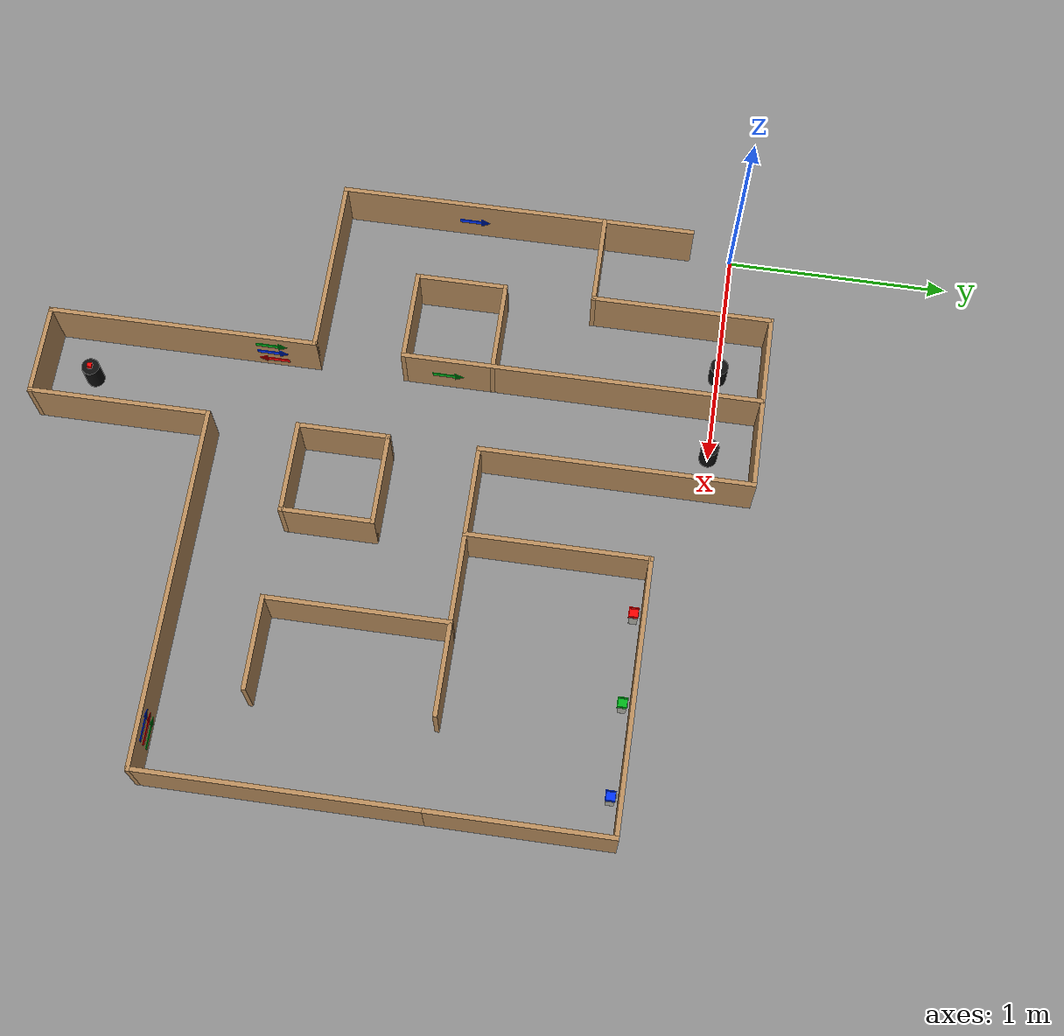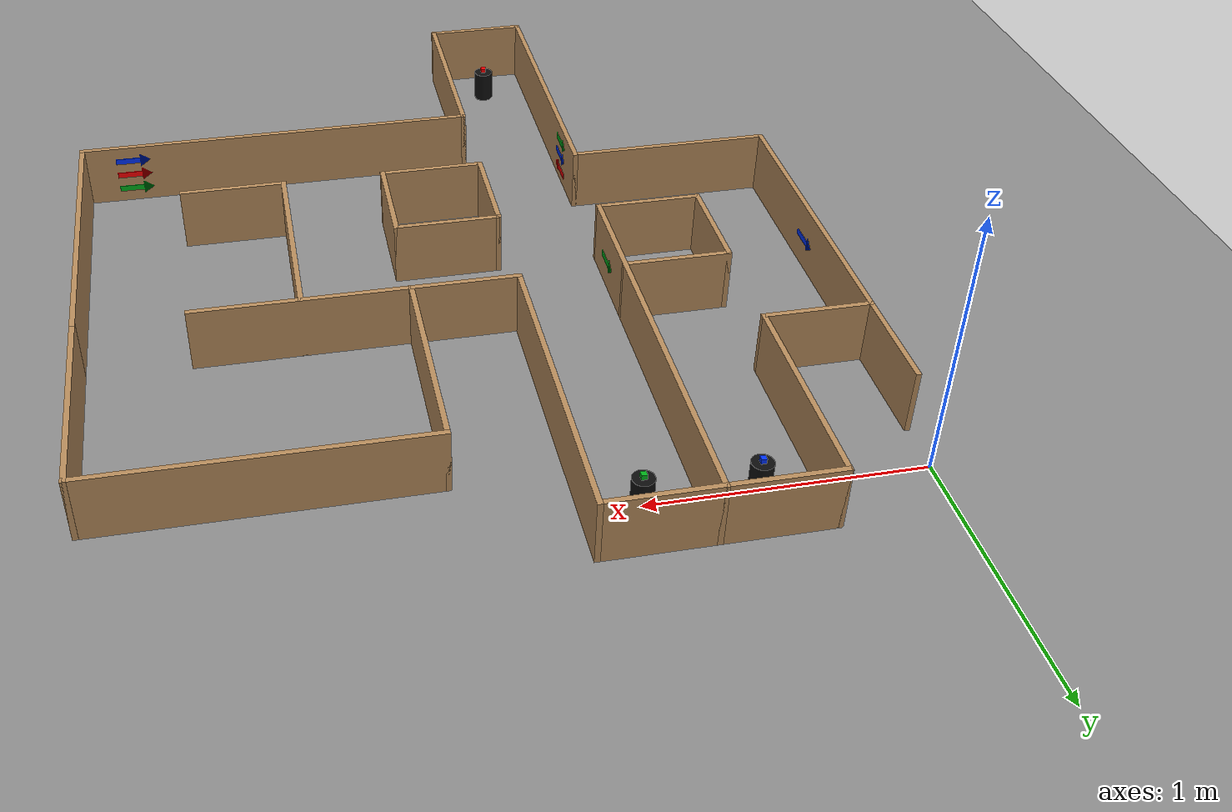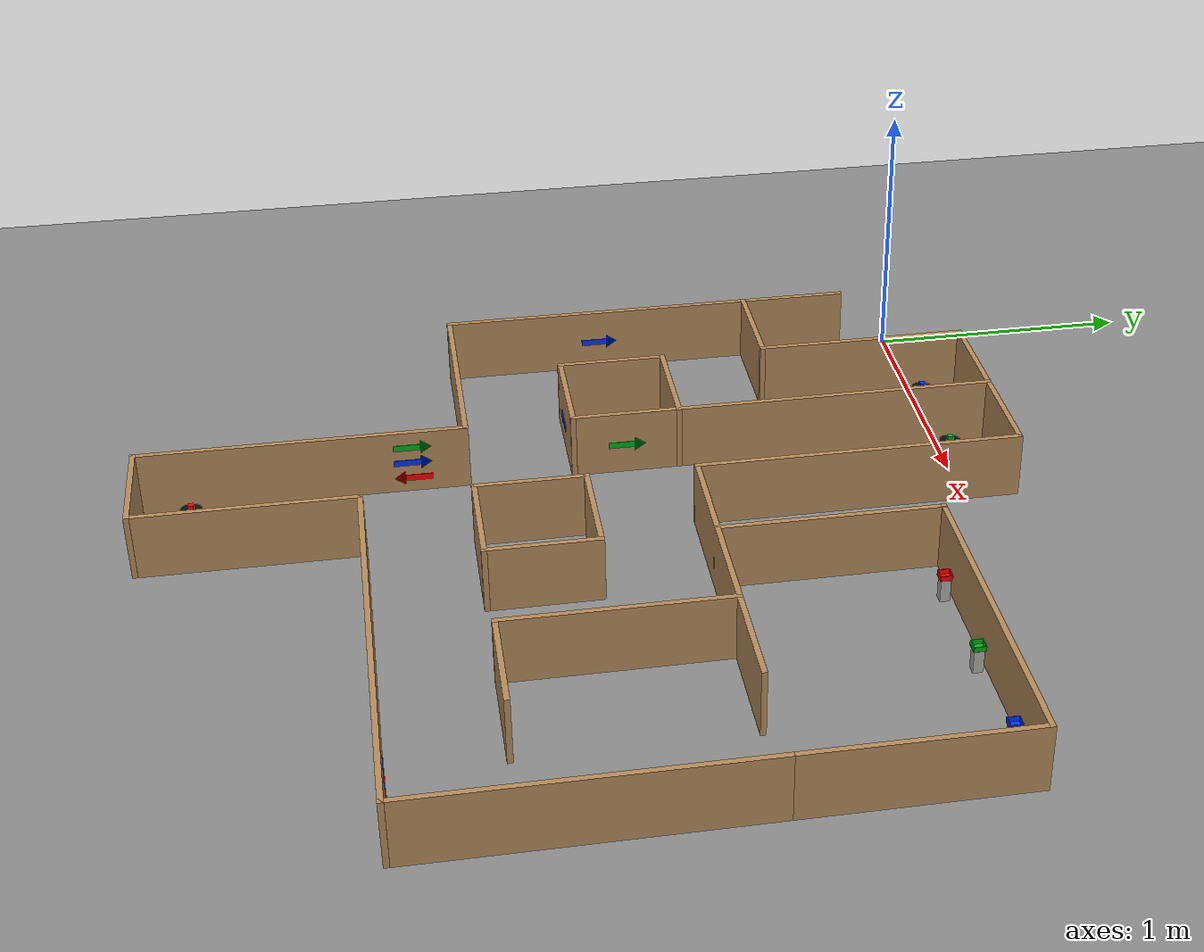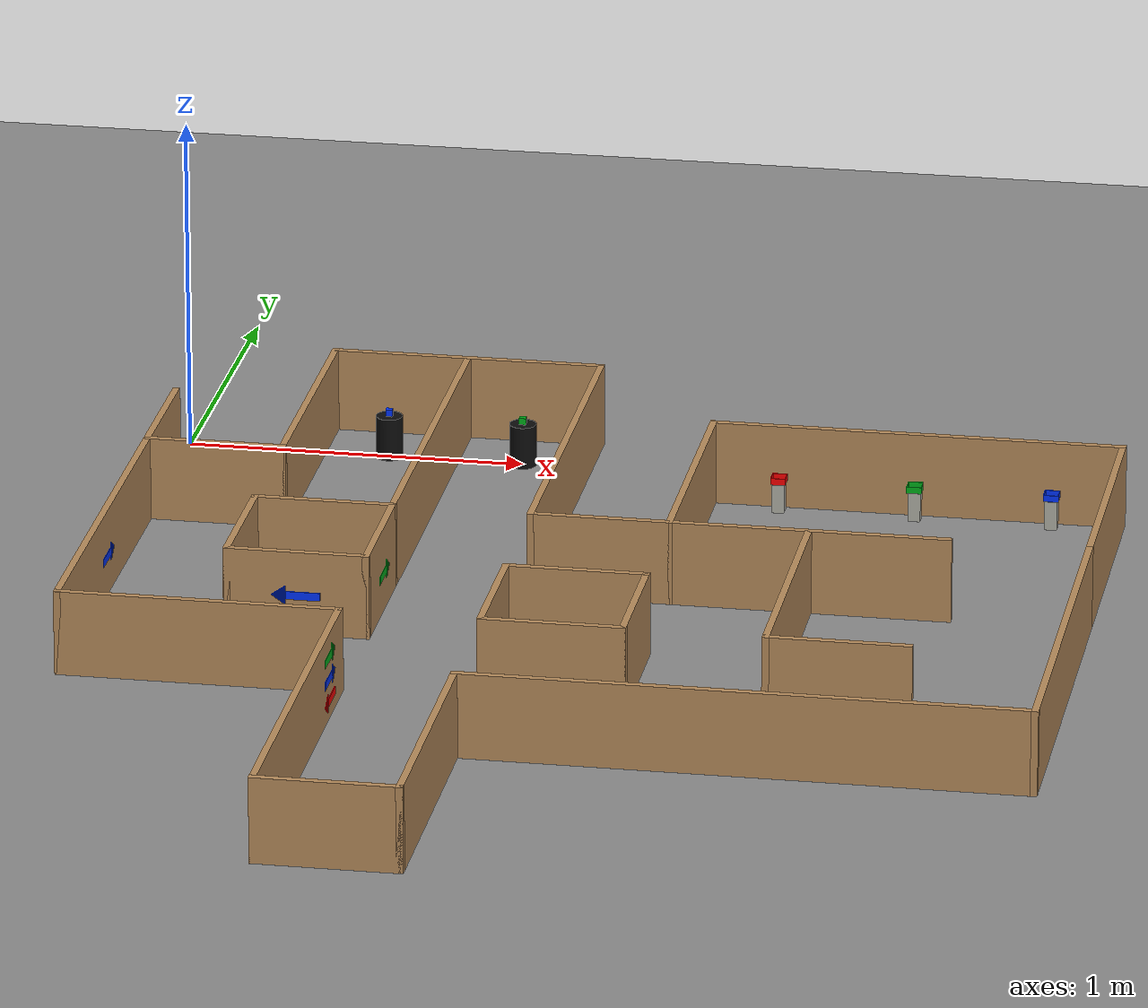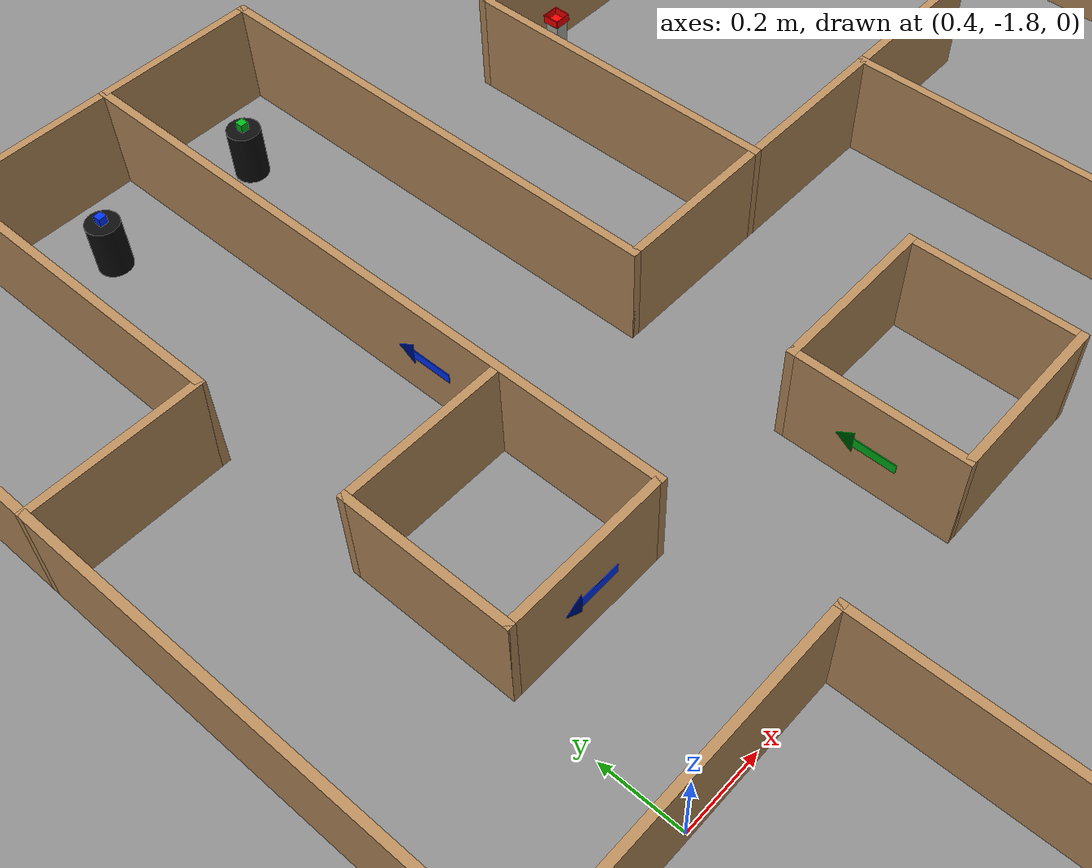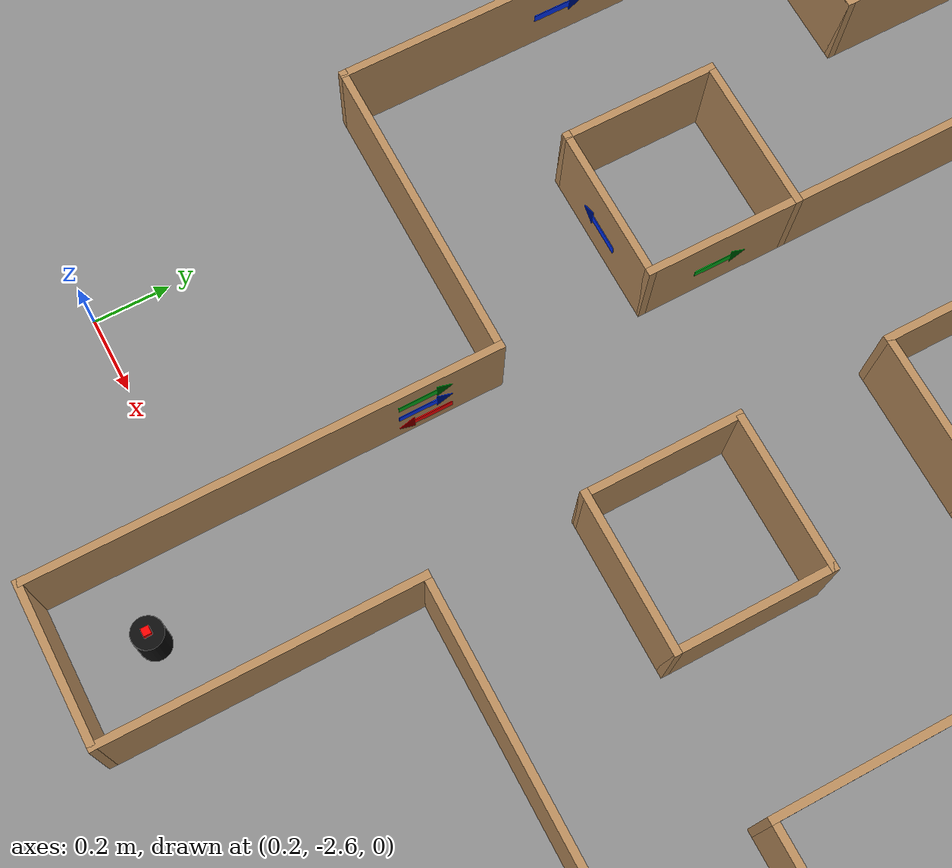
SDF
<?xml version="1.0"?>
<!-- Generado por tools/sim/mundo_cudar.py. No editar a mano. -->
<!-- Inicio del robot: x=2.6 y=-0.8 yaw=-1.5708 -->
<sdf version="1.9">
  <world name="ros2_world">

    <plugin filename="gz-sim-physics-system"
            name="gz::sim::systems::Physics"/>

    <plugin filename="gz-sim-user-commands-system"
            name="gz::sim::systems::UserCommands"/>

    <plugin filename="gz-sim-scene-broadcaster-system"
            name="gz::sim::systems::SceneBroadcaster"/>

    <plugin filename="gz-sim-sensors-system"
            name="gz::sim::systems::Sensors">
      <render_engine>ogre2</render_engine>
    </plugin>

    <light type="directional" name="sun">
      <pose>0 0 10 0 0 0</pose>
      <diffuse>0.8 0.8 0.8 1</diffuse>
      <specular>0.2 0.2 0.2 1</specular>
      <direction>-0.5 0.1 -0.9</direction>
    </light>

    <model name="ground_plane">
      <static>true</static>
      <link name="link">
        <collision name="collision">
          <geometry><plane><normal>0 0 1</normal><size>10 10</size></plane></geometry>
        </collision>
        <visual name="visual">
          <geometry><plane><normal>0 0 1</normal><size>10 10</size></plane></geometry>
          <material>
            <ambient>0.55 0.55 0.55 1</ambient>
            <diffuse>0.55 0.55 0.55 1</diffuse>
          </material>
        </visual>
      </link>
    </model>

    <model name="paredes">
      <static>true</static>
      <pose>0 0 0 0 0 0</pose>
      <link name="link">
        <collision name="c1"><pose>0.8 0.2 0.125 0 0 0</pose><geometry><box><size>0.82 0.02 0.25</size></box></geometry></collision>
        <visual name="v1"><pose>0.8 0.2 0.125 0 0 0</pose><geometry><box><size>0.82 0.02 0.25</size></box></geometry>
          <material>
            <ambient>0.72 0.55 0.36 1</ambient>
            <diffuse>0.72 0.55 0.36 1</diffuse>
          </material>
        </visual>
        <collision name="c2"><pose>0.4 -0.2 0.125 0 0 -1.5708</pose><geometry><box><size>0.82 0.02 0.25</size></box></geometry></collision>
        <visual name="v2"><pose>0.4 -0.2 0.125 0 0 -1.5708</pose><geometry><box><size>0.82 0.02 0.25</size></box></geometry>
          <material>
            <ambient>0.72 0.55 0.36 1</ambient>
            <diffuse>0.72 0.55 0.36 1</diffuse>
          </material>
        </visual>
        <collision name="c3"><pose>0.2 -0.6 0.125 0 0 0</pose><geometry><box><size>0.42 0.02 0.25</size></box></geometry></collision>
        <visual name="v3"><pose>0.2 -0.6 0.125 0 0 0</pose><geometry><box><size>0.42 0.02 0.25</size></box></geometry>
          <material>
            <ambient>0.72 0.55 0.36 1</ambient>
            <diffuse>0.72 0.55 0.36 1</diffuse>
          </material>
        </visual>
        <collision name="c4"><pose>0 -1 0.125 0 0 -1.5708</pose><geometry><box><size>1.62 0.02 0.25</size></box></geometry></collision>
        <visual name="v4"><pose>0 -1 0.125 0 0 -1.5708</pose><geometry><box><size>1.62 0.02 0.25</size></box></geometry>
          <material>
            <ambient>0.72 0.55 0.36 1</ambient>
            <diffuse>0.72 0.55 0.36 1</diffuse>
          </material>
        </visual>
        <collision name="c5"><pose>0.8 -0.6 0.125 0 0 -1.5708</pose><geometry><box><size>1.62 0.02 0.25</size></box></geometry></collision>
        <visual name="v5"><pose>0.8 -0.6 0.125 0 0 -1.5708</pose><geometry><box><size>1.62 0.02 0.25</size></box></geometry>
          <material>
            <ambient>0.72 0.55 0.36 1</ambient>
            <diffuse>0.72 0.55 0.36 1</diffuse>
          </material>
        </visual>
        <collision name="c6"><pose>0.6 -1 0.125 0 0 0</pose><geometry><box><size>0.42 0.02 0.25</size></box></geometry></collision>
        <visual name="v6"><pose>0.6 -1 0.125 0 0 0</pose><geometry><box><size>0.42 0.02 0.25</size></box></geometry>
          <material>
            <ambient>0.72 0.55 0.36 1</ambient>
            <diffuse>0.72 0.55 0.36 1</diffuse>
          </material>
        </visual>
        <collision name="c7"><pose>0.4 -1.2 0.125 0 0 -1.5708</pose><geometry><box><size>0.42 0.02 0.25</size></box></geometry></collision>
        <visual name="v7"><pose>0.4 -1.2 0.125 0 0 -1.5708</pose><geometry><box><size>0.42 0.02 0.25</size></box></geometry>
          <material>
            <ambient>0.72 0.55 0.36 1</ambient>
            <diffuse>0.72 0.55 0.36 1</diffuse>
          </material>
        </visual>
        <collision name="c8"><pose>0.6 -1.4 0.125 0 0 0</pose><geometry><box><size>0.42 0.02 0.25</size></box></geometry></collision>
        <visual name="v8"><pose>0.6 -1.4 0.125 0 0 0</pose><geometry><box><size>0.42 0.02 0.25</size></box></geometry>
          <material>
            <ambient>0.72 0.55 0.36 1</ambient>
            <diffuse>0.72 0.55 0.36 1</diffuse>
          </material>
        </visual>
        <collision name="c9"><pose>1.2 -0.4 0.125 0 0 -1.5708</pose><geometry><box><size>1.22 0.02 0.25</size></box></geometry></collision>
        <visual name="v9"><pose>1.2 -0.4 0.125 0 0 -1.5708</pose><geometry><box><size>1.22 0.02 0.25</size></box></geometry>
          <material>
            <ambient>0.72 0.55 0.36 1</ambient>
            <diffuse>0.72 0.55 0.36 1</diffuse>
          </material>
        </visual>
        <collision name="c10"><pose>1.8 -1 0.125 0 0 0</pose><geometry><box><size>1.22 0.02 0.25</size></box></geometry></collision>
        <visual name="v10"><pose>1.8 -1 0.125 0 0 0</pose><geometry><box><size>1.22 0.02 0.25</size></box></geometry>
          <material>
            <ambient>0.72 0.55 0.36 1</ambient>
            <diffuse>0.72 0.55 0.36 1</diffuse>
          </material>
        </visual>
        <collision name="c11"><pose>2 -1.4 0.125 0 0 -1.5708</pose><geometry><box><size>0.82 0.02 0.25</size></box></geometry></collision>
        <visual name="v11"><pose>2 -1.4 0.125 0 0 -1.5708</pose><geometry><box><size>0.82 0.02 0.25</size></box></geometry>
          <material>
            <ambient>0.72 0.55 0.36 1</ambient>
            <diffuse>0.72 0.55 0.36 1</diffuse>
          </material>
        </visual>
        <collision name="c12"><pose>2.2 -1.8 0.125 0 0 0</pose><geometry><box><size>0.42 0.02 0.25</size></box></geometry></collision>
        <visual name="v12"><pose>2.2 -1.8 0.125 0 0 0</pose><geometry><box><size>0.42 0.02 0.25</size></box></geometry>
          <material>
            <ambient>0.72 0.55 0.36 1</ambient>
            <diffuse>0.72 0.55 0.36 1</diffuse>
          </material>
        </visual>
        <collision name="c13"><pose>2.8 -1.6 0.125 0 0 -1.5708</pose><geometry><box><size>1.22 0.02 0.25</size></box></geometry></collision>
        <visual name="v13"><pose>2.8 -1.6 0.125 0 0 -1.5708</pose><geometry><box><size>1.22 0.02 0.25</size></box></geometry>
          <material>
            <ambient>0.72 0.55 0.36 1</ambient>
            <diffuse>0.72 0.55 0.36 1</diffuse>
          </material>
        </visual>
        <collision name="c14"><pose>1.4 -1.4 0.125 0 0 0</pose><geometry><box><size>0.42 0.02 0.25</size></box></geometry></collision>
        <visual name="v14"><pose>1.4 -1.4 0.125 0 0 0</pose><geometry><box><size>0.42 0.02 0.25</size></box></geometry>
          <material>
            <ambient>0.72 0.55 0.36 1</ambient>
            <diffuse>0.72 0.55 0.36 1</diffuse>
          </material>
        </visual>
        <collision name="c15"><pose>1.6 -1.6 0.125 0 0 -1.5708</pose><geometry><box><size>0.42 0.02 0.25</size></box></geometry></collision>
        <visual name="v15"><pose>1.6 -1.6 0.125 0 0 -1.5708</pose><geometry><box><size>0.42 0.02 0.25</size></box></geometry>
          <material>
            <ambient>0.72 0.55 0.36 1</ambient>
            <diffuse>0.72 0.55 0.36 1</diffuse>
          </material>
        </visual>
        <collision name="c16"><pose>1.4 -1.8 0.125 0 0 0</pose><geometry><box><size>0.42 0.02 0.25</size></box></geometry></collision>
        <visual name="v16"><pose>1.4 -1.8 0.125 0 0 0</pose><geometry><box><size>0.42 0.02 0.25</size></box></geometry>
          <material>
            <ambient>0.72 0.55 0.36 1</ambient>
            <diffuse>0.72 0.55 0.36 1</diffuse>
          </material>
        </visual>
        <collision name="c17"><pose>1.2 -1.6 0.125 0 0 -1.5708</pose><geometry><box><size>0.42 0.02 0.25</size></box></geometry></collision>
        <visual name="v17"><pose>1.2 -1.6 0.125 0 0 -1.5708</pose><geometry><box><size>0.42 0.02 0.25</size></box></geometry>
          <material>
            <ambient>0.72 0.55 0.36 1</ambient>
            <diffuse>0.72 0.55 0.36 1</diffuse>
          </material>
        </visual>
        <collision name="c18"><pose>0.4 -1.8 0.125 0 0 0</pose><geometry><box><size>0.82 0.02 0.25</size></box></geometry></collision>
        <visual name="v18"><pose>0.4 -1.8 0.125 0 0 0</pose><geometry><box><size>0.82 0.02 0.25</size></box></geometry>
          <material>
            <ambient>0.72 0.55 0.36 1</ambient>
            <diffuse>0.72 0.55 0.36 1</diffuse>
          </material>
        </visual>
        <collision name="c19"><pose>0.8 -2.4 0.125 0 0 -1.5708</pose><geometry><box><size>1.22 0.02 0.25</size></box></geometry></collision>
        <visual name="v19"><pose>0.8 -2.4 0.125 0 0 -1.5708</pose><geometry><box><size>1.22 0.02 0.25</size></box></geometry>
          <material>
            <ambient>0.72 0.55 0.36 1</ambient>
            <diffuse>0.72 0.55 0.36 1</diffuse>
          </material>
        </visual>
        <collision name="c20"><pose>1 -3 0.125 0 0 0</pose><geometry><box><size>0.42 0.02 0.25</size></box></geometry></collision>
        <visual name="v20"><pose>1 -3 0.125 0 0 0</pose><geometry><box><size>0.42 0.02 0.25</size></box></geometry>
          <material>
            <ambient>0.72 0.55 0.36 1</ambient>
            <diffuse>0.72 0.55 0.36 1</diffuse>
          </material>
        </visual>
        <collision name="c21"><pose>1.2 -2.6 0.125 0 0 -1.5708</pose><geometry><box><size>0.82 0.02 0.25</size></box></geometry></collision>
        <visual name="v21"><pose>1.2 -2.6 0.125 0 0 -1.5708</pose><geometry><box><size>0.82 0.02 0.25</size></box></geometry>
          <material>
            <ambient>0.72 0.55 0.36 1</ambient>
            <diffuse>0.72 0.55 0.36 1</diffuse>
          </material>
        </visual>
        <collision name="c22"><pose>2 -2.2 0.125 0 0 0</pose><geometry><box><size>1.62 0.02 0.25</size></box></geometry></collision>
        <visual name="v22"><pose>2 -2.2 0.125 0 0 0</pose><geometry><box><size>1.62 0.02 0.25</size></box></geometry>
          <material>
            <ambient>0.72 0.55 0.36 1</ambient>
            <diffuse>0.72 0.55 0.36 1</diffuse>
          </material>
        </visual>
        <collision name="c23"><pose>2.2 -0.2 0.125 0 0 0</pose><geometry><box><size>1.22 0.02 0.25</size></box></geometry></collision>
        <visual name="v23"><pose>2.2 -0.2 0.125 0 0 0</pose><geometry><box><size>1.22 0.02 0.25</size></box></geometry>
          <material>
            <ambient>0.72 0.55 0.36 1</ambient>
            <diffuse>0.72 0.55 0.36 1</diffuse>
          </material>
        </visual>
        <collision name="c24"><pose>1.6 -0.6 0.125 0 0 -1.5708</pose><geometry><box><size>0.82 0.02 0.25</size></box></geometry></collision>
        <visual name="v24"><pose>1.6 -0.6 0.125 0 0 -1.5708</pose><geometry><box><size>0.82 0.02 0.25</size></box></geometry>
          <material>
            <ambient>0.72 0.55 0.36 1</ambient>
            <diffuse>0.72 0.55 0.36 1</diffuse>
          </material>
        </visual>
        <collision name="c25"><pose>2.8 -0.6 0.125 0 0 -1.5708</pose><geometry><box><size>0.82 0.02 0.25</size></box></geometry></collision>
        <visual name="v25"><pose>2.8 -0.6 0.125 0 0 -1.5708</pose><geometry><box><size>0.82 0.02 0.25</size></box></geometry>
          <material>
            <ambient>0.72 0.55 0.36 1</ambient>
            <diffuse>0.72 0.55 0.36 1</diffuse>
          </material>
        </visual>
      </link>
    </model>

    <model name="soporte_cubo_azul">
      <static>true</static>
      <pose>0.6 0 0.06425 0 0 0</pose>
      <link name="link">
        <collision name="colision">
          <geometry><cylinder><radius>0.04</radius><length>0.1285</length></cylinder></geometry>
        </collision>
        <visual name="visual">
          <geometry><cylinder><radius>0.04</radius><length>0.1285</length></cylinder></geometry>
          <material>
            <ambient>0.05 0.05 0.05 1</ambient>
            <diffuse>0.05 0.05 0.05 1</diffuse>
          </material>
        </visual>
      </link>
    </model>

    <model name="cubo_azul">
      <pose>0.6 0 0.1387 0 0 0</pose>
      <link name="link">
        <inertial>
          <mass>0.0099</mass>
          <inertia>
            <ixx>6.6000e-07</ixx><iyy>6.6000e-07</iyy><izz>6.6000e-07</izz><ixy>0</ixy><ixz>0</ixz><iyz>0</iyz>
          </inertia>
        </inertial>
        <collision name="colision">
          <pose>0 0 0 0 0 0</pose>
          <geometry><box><size>0.02 0.02 0.02</size></box></geometry>
          <surface><friction><ode><mu>1</mu><mu2>1</mu2></ode></friction></surface>
        </collision>
        <visual name="visual">
          <pose>0 0 0 0 0 0</pose>
          <geometry><box><size>0.02 0.02 0.02</size></box></geometry>
          <material>
            <ambient>0 0.2 1 1</ambient>
            <diffuse>0 0.2 1 1</diffuse>
          </material>
        </visual>
      </link>
    </model>

    <model name="soporte_cubo_verde">
      <static>true</static>
      <pose>1 0 0.06425 0 0 0</pose>
      <link name="link">
        <collision name="colision">
          <geometry><cylinder><radius>0.04</radius><length>0.1285</length></cylinder></geometry>
        </collision>
        <visual name="visual">
          <geometry><cylinder><radius>0.04</radius><length>0.1285</length></cylinder></geometry>
          <material>
            <ambient>0.05 0.05 0.05 1</ambient>
            <diffuse>0.05 0.05 0.05 1</diffuse>
          </material>
        </visual>
      </link>
    </model>

    <model name="cubo_verde">
      <pose>1 0 0.1387 0 0 0</pose>
      <link name="link">
        <inertial>
          <mass>0.0099</mass>
          <inertia>
            <ixx>6.6000e-07</ixx><iyy>6.6000e-07</iyy><izz>6.6000e-07</izz><ixy>0</ixy><ixz>0</ixz><iyz>0</iyz>
          </inertia>
        </inertial>
        <collision name="colision">
          <pose>0 0 0 0 0 0</pose>
          <geometry><box><size>0.02 0.02 0.02</size></box></geometry>
          <surface><friction><ode><mu>1</mu><mu2>1</mu2></ode></friction></surface>
        </collision>
        <visual name="visual">
          <pose>0 0 0 0 0 0</pose>
          <geometry><box><size>0.02 0.02 0.02</size></box></geometry>
          <material>
            <ambient>0 0.7 0.1 1</ambient>
            <diffuse>0 0.7 0.1 1</diffuse>
          </material>
        </visual>
      </link>
    </model>

    <model name="soporte_cubo_rojo">
      <static>true</static>
      <pose>1 -2.8 0.06425 0 0 0</pose>
      <link name="link">
        <collision name="colision">
          <geometry><cylinder><radius>0.04</radius><length>0.1285</length></cylinder></geometry>
        </collision>
        <visual name="visual">
          <geometry><cylinder><radius>0.04</radius><length>0.1285</length></cylinder></geometry>
          <material>
            <ambient>0.05 0.05 0.05 1</ambient>
            <diffuse>0.05 0.05 0.05 1</diffuse>
          </material>
        </visual>
      </link>
    </model>

    <model name="cubo_rojo">
      <pose>1 -2.8 0.1387 0 0 0</pose>
      <link name="link">
        <inertial>
          <mass>0.0099</mass>
          <inertia>
            <ixx>6.6000e-07</ixx><iyy>6.6000e-07</iyy><izz>6.6000e-07</izz><ixy>0</ixy><ixz>0</ixz><iyz>0</iyz>
          </inertia>
        </inertial>
        <collision name="colision">
          <pose>0 0 0 0 0 0</pose>
          <geometry><box><size>0.02 0.02 0.02</size></box></geometry>
          <surface><friction><ode><mu>1</mu><mu2>1</mu2></ode></friction></surface>
        </collision>
        <visual name="visual">
          <pose>0 0 0 0 0 0</pose>
          <geometry><box><size>0.02 0.02 0.02</size></box></geometry>
          <material>
            <ambient>1 0 0 1</ambient>
            <diffuse>1 0 0 1</diffuse>
          </material>
        </visual>
      </link>
    </model>

    <model name="soporte_canasto_rojo">
      <static>true</static>
      <pose>1.8 -0.242 0.04425 0 0 0</pose>
      <link name="link">
        <collision name="colision">
          <pose>0 0 0 0 0 0</pose>
          <geometry><box><size>0.036 0.036 0.0885</size></box></geometry>
        </collision>
        <visual name="visual">
          <pose>0 0 0 0 0 0</pose>
          <geometry><box><size>0.036 0.036 0.0885</size></box></geometry>
          <material>
            <ambient>0.7 0.7 0.66 1</ambient>
            <diffuse>0.7 0.7 0.66 1</diffuse>
          </material>
        </visual>
      </link>
    </model>

    <model name="canasto_rojo">
      <static>true</static>
      <pose>1.8 -0.242 0.0885 0 0 0</pose>
      <link name="link">
        <collision name="c_fondo">
          <pose>0 0 0.0005 0 0 0</pose>
          <geometry><box><size>0.044 0.044 0.001</size></box></geometry>
          <surface><friction><ode><mu>1</mu><mu2>1</mu2></ode></friction></surface>
        </collision>
        <visual name="v_fondo">
          <pose>0 0 0.0005 0 0 0</pose>
          <geometry><box><size>0.044 0.044 0.001</size></box></geometry>
          <material>
            <ambient>1 0 0 1</ambient>
            <diffuse>1 0 0 1</diffuse>
          </material>
        </visual>
        <collision name="c_pared_n">
          <pose>0 0.021 0.01 0 0 0</pose>
          <geometry><box><size>0.044 0.002 0.02</size></box></geometry>
          <surface><friction><ode><mu>1</mu><mu2>1</mu2></ode></friction></surface>
        </collision>
        <visual name="v_pared_n">
          <pose>0 0.021 0.01 0 0 0</pose>
          <geometry><box><size>0.044 0.002 0.02</size></box></geometry>
          <material>
            <ambient>1 0 0 1</ambient>
            <diffuse>1 0 0 1</diffuse>
          </material>
        </visual>
        <collision name="c_pared_s">
          <pose>0 -0.021 0.01 0 0 0</pose>
          <geometry><box><size>0.044 0.002 0.02</size></box></geometry>
          <surface><friction><ode><mu>1</mu><mu2>1</mu2></ode></friction></surface>
        </collision>
        <visual name="v_pared_s">
          <pose>0 -0.021 0.01 0 0 0</pose>
          <geometry><box><size>0.044 0.002 0.02</size></box></geometry>
          <material>
            <ambient>1 0 0 1</ambient>
            <diffuse>1 0 0 1</diffuse>
          </material>
        </visual>
        <collision name="c_pared_e">
          <pose>0.021 0 0.01 0 0 0</pose>
          <geometry><box><size>0.002 0.04 0.02</size></box></geometry>
          <surface><friction><ode><mu>1</mu><mu2>1</mu2></ode></friction></surface>
        </collision>
        <visual name="v_pared_e">
          <pose>0.021 0 0.01 0 0 0</pose>
          <geometry><box><size>0.002 0.04 0.02</size></box></geometry>
          <material>
            <ambient>1 0 0 1</ambient>
            <diffuse>1 0 0 1</diffuse>
          </material>
        </visual>
        <collision name="c_pared_o">
          <pose>-0.021 0 0.01 0 0 0</pose>
          <geometry><box><size>0.002 0.04 0.02</size></box></geometry>
          <surface><friction><ode><mu>1</mu><mu2>1</mu2></ode></friction></surface>
        </collision>
        <visual name="v_pared_o">
          <pose>-0.021 0 0.01 0 0 0</pose>
          <geometry><box><size>0.002 0.04 0.02</size></box></geometry>
          <material>
            <ambient>1 0 0 1</ambient>
            <diffuse>1 0 0 1</diffuse>
          </material>
        </visual>
      </link>
    </model>

    <model name="soporte_canasto_verde">
      <static>true</static>
      <pose>2.2 -0.242 0.04425 0 0 0</pose>
      <link name="link">
        <collision name="colision">
          <pose>0 0 0 0 0 0</pose>
          <geometry><box><size>0.036 0.036 0.0885</size></box></geometry>
        </collision>
        <visual name="visual">
          <pose>0 0 0 0 0 0</pose>
          <geometry><box><size>0.036 0.036 0.0885</size></box></geometry>
          <material>
            <ambient>0.7 0.7 0.66 1</ambient>
            <diffuse>0.7 0.7 0.66 1</diffuse>
          </material>
        </visual>
      </link>
    </model>

    <model name="canasto_verde">
      <static>true</static>
      <pose>2.2 -0.242 0.0885 0 0 0</pose>
      <link name="link">
        <collision name="c_fondo">
          <pose>0 0 0.0005 0 0 0</pose>
          <geometry><box><size>0.044 0.044 0.001</size></box></geometry>
          <surface><friction><ode><mu>1</mu><mu2>1</mu2></ode></friction></surface>
        </collision>
        <visual name="v_fondo">
          <pose>0 0 0.0005 0 0 0</pose>
          <geometry><box><size>0.044 0.044 0.001</size></box></geometry>
          <material>
            <ambient>0 0.7 0.1 1</ambient>
            <diffuse>0 0.7 0.1 1</diffuse>
          </material>
        </visual>
        <collision name="c_pared_n">
          <pose>0 0.021 0.01 0 0 0</pose>
          <geometry><box><size>0.044 0.002 0.02</size></box></geometry>
          <surface><friction><ode><mu>1</mu><mu2>1</mu2></ode></friction></surface>
        </collision>
        <visual name="v_pared_n">
          <pose>0 0.021 0.01 0 0 0</pose>
          <geometry><box><size>0.044 0.002 0.02</size></box></geometry>
          <material>
            <ambient>0 0.7 0.1 1</ambient>
            <diffuse>0 0.7 0.1 1</diffuse>
          </material>
        </visual>
        <collision name="c_pared_s">
          <pose>0 -0.021 0.01 0 0 0</pose>
          <geometry><box><size>0.044 0.002 0.02</size></box></geometry>
          <surface><friction><ode><mu>1</mu><mu2>1</mu2></ode></friction></surface>
        </collision>
        <visual name="v_pared_s">
          <pose>0 -0.021 0.01 0 0 0</pose>
          <geometry><box><size>0.044 0.002 0.02</size></box></geometry>
          <material>
            <ambient>0 0.7 0.1 1</ambient>
            <diffuse>0 0.7 0.1 1</diffuse>
          </material>
        </visual>
        <collision name="c_pared_e">
          <pose>0.021 0 0.01 0 0 0</pose>
          <geometry><box><size>0.002 0.04 0.02</size></box></geometry>
          <surface><friction><ode><mu>1</mu><mu2>1</mu2></ode></friction></surface>
        </collision>
        <visual name="v_pared_e">
          <pose>0.021 0 0.01 0 0 0</pose>
          <geometry><box><size>0.002 0.04 0.02</size></box></geometry>
          <material>
            <ambient>0 0.7 0.1 1</ambient>
            <diffuse>0 0.7 0.1 1</diffuse>
          </material>
        </visual>
        <collision name="c_pared_o">
          <pose>-0.021 0 0.01 0 0 0</pose>
          <geometry><box><size>0.002 0.04 0.02</size></box></geometry>
          <surface><friction><ode><mu>1</mu><mu2>1</mu2></ode></friction></surface>
        </collision>
        <visual name="v_pared_o">
          <pose>-0.021 0 0.01 0 0 0</pose>
          <geometry><box><size>0.002 0.04 0.02</size></box></geometry>
          <material>
            <ambient>0 0.7 0.1 1</ambient>
            <diffuse>0 0.7 0.1 1</diffuse>
          </material>
        </visual>
      </link>
    </model>

    <model name="soporte_canasto_azul">
      <static>true</static>
      <pose>2.6 -0.242 0.04425 0 0 0</pose>
      <link name="link">
        <collision name="colision">
          <pose>0 0 0 0 0 0</pose>
          <geometry><box><size>0.036 0.036 0.0885</size></box></geometry>
        </collision>
        <visual name="visual">
          <pose>0 0 0 0 0 0</pose>
          <geometry><box><size>0.036 0.036 0.0885</size></box></geometry>
          <material>
            <ambient>0.7 0.7 0.66 1</ambient>
            <diffuse>0.7 0.7 0.66 1</diffuse>
          </material>
        </visual>
      </link>
    </model>

    <model name="canasto_azul">
      <static>true</static>
      <pose>2.6 -0.242 0.0885 0 0 0</pose>
      <link name="link">
        <collision name="c_fondo">
          <pose>0 0 0.0005 0 0 0</pose>
          <geometry><box><size>0.044 0.044 0.001</size></box></geometry>
          <surface><friction><ode><mu>1</mu><mu2>1</mu2></ode></friction></surface>
        </collision>
        <visual name="v_fondo">
          <pose>0 0 0.0005 0 0 0</pose>
          <geometry><box><size>0.044 0.044 0.001</size></box></geometry>
          <material>
            <ambient>0 0.2 1 1</ambient>
            <diffuse>0 0.2 1 1</diffuse>
          </material>
        </visual>
        <collision name="c_pared_n">
          <pose>0 0.021 0.01 0 0 0</pose>
          <geometry><box><size>0.044 0.002 0.02</size></box></geometry>
          <surface><friction><ode><mu>1</mu><mu2>1</mu2></ode></friction></surface>
        </collision>
        <visual name="v_pared_n">
          <pose>0 0.021 0.01 0 0 0</pose>
          <geometry><box><size>0.044 0.002 0.02</size></box></geometry>
          <material>
            <ambient>0 0.2 1 1</ambient>
            <diffuse>0 0.2 1 1</diffuse>
          </material>
        </visual>
        <collision name="c_pared_s">
          <pose>0 -0.021 0.01 0 0 0</pose>
          <geometry><box><size>0.044 0.002 0.02</size></box></geometry>
          <surface><friction><ode><mu>1</mu><mu2>1</mu2></ode></friction></surface>
        </collision>
        <visual name="v_pared_s">
          <pose>0 -0.021 0.01 0 0 0</pose>
          <geometry><box><size>0.044 0.002 0.02</size></box></geometry>
          <material>
            <ambient>0 0.2 1 1</ambient>
            <diffuse>0 0.2 1 1</diffuse>
          </material>
        </visual>
        <collision name="c_pared_e">
          <pose>0.021 0 0.01 0 0 0</pose>
          <geometry><box><size>0.002 0.04 0.02</size></box></geometry>
          <surface><friction><ode><mu>1</mu><mu2>1</mu2></ode></friction></surface>
        </collision>
        <visual name="v_pared_e">
          <pose>0.021 0 0.01 0 0 0</pose>
          <geometry><box><size>0.002 0.04 0.02</size></box></geometry>
          <material>
            <ambient>0 0.2 1 1</ambient>
            <diffuse>0 0.2 1 1</diffuse>
          </material>
        </visual>
        <collision name="c_pared_o">
          <pose>-0.021 0 0.01 0 0 0</pose>
          <geometry><box><size>0.002 0.04 0.02</size></box></geometry>
          <surface><friction><ode><mu>1</mu><mu2>1</mu2></ode></friction></surface>
        </collision>
        <visual name="v_pared_o">
          <pose>-0.021 0 0.01 0 0 0</pose>
          <geometry><box><size>0.002 0.04 0.02</size></box></geometry>
          <material>
            <ambient>0 0.2 1 1</ambient>
            <diffuse>0 0.2 1 1</diffuse>
          </material>
        </visual>
      </link>
    </model>

    <model name="flechas">
      <static>true</static>
      <link name="flecha_0">
        <pose>2.6 -2.186 0.19 0 0 3.14159</pose>
        <visual name="p0">
          <pose>-0.02 0 0 0 0 0</pose>
          <geometry><box><size>0.1 0.002 0.024</size></box></geometry>
          <material>
            <ambient>0 0.2 1 1</ambient>
            <diffuse>0 0.2 1 1</diffuse>
          </material>
        </visual>
        <visual name="p1">
          <pose>0.0308 0 0 0 0 0</pose>
          <geometry><box><size>0.0016 0.002 0.056</size></box></geometry>
          <material>
            <ambient>0 0.2 1 1</ambient>
            <diffuse>0 0.2 1 1</diffuse>
          </material>
        </visual>
        <visual name="p2">
          <pose>0.0324 0 0 0 0 0</pose>
          <geometry><box><size>0.0016 0.002 0.05376</size></box></geometry>
          <material>
            <ambient>0 0.2 1 1</ambient>
            <diffuse>0 0.2 1 1</diffuse>
          </material>
        </visual>
        <visual name="p3">
          <pose>0.034 0 0 0 0 0</pose>
          <geometry><box><size>0.0016 0.002 0.05152</size></box></geometry>
          <material>
            <ambient>0 0.2 1 1</ambient>
            <diffuse>0 0.2 1 1</diffuse>
          </material>
        </visual>
        <visual name="p4">
          <pose>0.0356 0 0 0 0 0</pose>
          <geometry><box><size>0.0016 0.002 0.04928</size></box></geometry>
          <material>
            <ambient>0 0.2 1 1</ambient>
            <diffuse>0 0.2 1 1</diffuse>
          </material>
        </visual>
        <visual name="p5">
          <pose>0.0372 0 0 0 0 0</pose>
          <geometry><box><size>0.0016 0.002 0.04704</size></box></geometry>
          <material>
            <ambient>0 0.2 1 1</ambient>
            <diffuse>0 0.2 1 1</diffuse>
          </material>
        </visual>
        <visual name="p6">
          <pose>0.0388 0 0 0 0 0</pose>
          <geometry><box><size>0.0016 0.002 0.0448</size></box></geometry>
          <material>
            <ambient>0 0.2 1 1</ambient>
            <diffuse>0 0.2 1 1</diffuse>
          </material>
        </visual>
        <visual name="p7">
          <pose>0.0404 0 0 0 0 0</pose>
          <geometry><box><size>0.0016 0.002 0.04256</size></box></geometry>
          <material>
            <ambient>0 0.2 1 1</ambient>
            <diffuse>0 0.2 1 1</diffuse>
          </material>
        </visual>
        <visual name="p8">
          <pose>0.042 0 0 0 0 0</pose>
          <geometry><box><size>0.0016 0.002 0.04032</size></box></geometry>
          <material>
            <ambient>0 0.2 1 1</ambient>
            <diffuse>0 0.2 1 1</diffuse>
          </material>
        </visual>
        <visual name="p9">
          <pose>0.0436 0 0 0 0 0</pose>
          <geometry><box><size>0.0016 0.002 0.03808</size></box></geometry>
          <material>
            <ambient>0 0.2 1 1</ambient>
            <diffuse>0 0.2 1 1</diffuse>
          </material>
        </visual>
        <visual name="p10">
          <pose>0.0452 0 0 0 0 0</pose>
          <geometry><box><size>0.0016 0.002 0.03584</size></box></geometry>
          <material>
            <ambient>0 0.2 1 1</ambient>
            <diffuse>0 0.2 1 1</diffuse>
          </material>
        </visual>
        <visual name="p11">
          <pose>0.0468 0 0 0 0 0</pose>
          <geometry><box><size>0.0016 0.002 0.0336</size></box></geometry>
          <material>
            <ambient>0 0.2 1 1</ambient>
            <diffuse>0 0.2 1 1</diffuse>
          </material>
        </visual>
        <visual name="p12">
          <pose>0.0484 0 0 0 0 0</pose>
          <geometry><box><size>0.0016 0.002 0.03136</size></box></geometry>
          <material>
            <ambient>0 0.2 1 1</ambient>
            <diffuse>0 0.2 1 1</diffuse>
          </material>
        </visual>
        <visual name="p13">
          <pose>0.05 0 0 0 0 0</pose>
          <geometry><box><size>0.0016 0.002 0.02912</size></box></geometry>
          <material>
            <ambient>0 0.2 1 1</ambient>
            <diffuse>0 0.2 1 1</diffuse>
          </material>
        </visual>
        <visual name="p14">
          <pose>0.0516 0 0 0 0 0</pose>
          <geometry><box><size>0.0016 0.002 0.02688</size></box></geometry>
          <material>
            <ambient>0 0.2 1 1</ambient>
            <diffuse>0 0.2 1 1</diffuse>
          </material>
        </visual>
        <visual name="p15">
          <pose>0.0532 0 0 0 0 0</pose>
          <geometry><box><size>0.0016 0.002 0.02464</size></box></geometry>
          <material>
            <ambient>0 0.2 1 1</ambient>
            <diffuse>0 0.2 1 1</diffuse>
          </material>
        </visual>
        <visual name="p16">
          <pose>0.0548 0 0 0 0 0</pose>
          <geometry><box><size>0.0016 0.002 0.0224</size></box></geometry>
          <material>
            <ambient>0 0.2 1 1</ambient>
            <diffuse>0 0.2 1 1</diffuse>
          </material>
        </visual>
        <visual name="p17">
          <pose>0.0564 0 0 0 0 0</pose>
          <geometry><box><size>0.0016 0.002 0.02016</size></box></geometry>
          <material>
            <ambient>0 0.2 1 1</ambient>
            <diffuse>0 0.2 1 1</diffuse>
          </material>
        </visual>
        <visual name="p18">
          <pose>0.058 0 0 0 0 0</pose>
          <geometry><box><size>0.0016 0.002 0.01792</size></box></geometry>
          <material>
            <ambient>0 0.2 1 1</ambient>
            <diffuse>0 0.2 1 1</diffuse>
          </material>
        </visual>
        <visual name="p19">
          <pose>0.0596 0 0 0 0 0</pose>
          <geometry><box><size>0.0016 0.002 0.01568</size></box></geometry>
          <material>
            <ambient>0 0.2 1 1</ambient>
            <diffuse>0 0.2 1 1</diffuse>
          </material>
        </visual>
        <visual name="p20">
          <pose>0.0612 0 0 0 0 0</pose>
          <geometry><box><size>0.0016 0.002 0.01344</size></box></geometry>
          <material>
            <ambient>0 0.2 1 1</ambient>
            <diffuse>0 0.2 1 1</diffuse>
          </material>
        </visual>
        <visual name="p21">
          <pose>0.0628 0 0 0 0 0</pose>
          <geometry><box><size>0.0016 0.002 0.0112</size></box></geometry>
          <material>
            <ambient>0 0.2 1 1</ambient>
            <diffuse>0 0.2 1 1</diffuse>
          </material>
        </visual>
        <visual name="p22">
          <pose>0.0644 0 0 0 0 0</pose>
          <geometry><box><size>0.0016 0.002 0.00896</size></box></geometry>
          <material>
            <ambient>0 0.2 1 1</ambient>
            <diffuse>0 0.2 1 1</diffuse>
          </material>
        </visual>
        <visual name="p23">
          <pose>0.066 0 0 0 0 0</pose>
          <geometry><box><size>0.0016 0.002 0.00672</size></box></geometry>
          <material>
            <ambient>0 0.2 1 1</ambient>
            <diffuse>0 0.2 1 1</diffuse>
          </material>
        </visual>
        <visual name="p24">
          <pose>0.0676 0 0 0 0 0</pose>
          <geometry><box><size>0.0016 0.002 0.00448</size></box></geometry>
          <material>
            <ambient>0 0.2 1 1</ambient>
            <diffuse>0 0.2 1 1</diffuse>
          </material>
        </visual>
        <visual name="p25">
          <pose>0.0692 0 0 0 0 0</pose>
          <geometry><box><size>0.0016 0.002 0.00224</size></box></geometry>
          <material>
            <ambient>0 0.2 1 1</ambient>
            <diffuse>0 0.2 1 1</diffuse>
          </material>
        </visual>
      </link>
      <link name="flecha_1">
        <pose>2.6 -2.186 0.125 0 0 3.14159</pose>
        <visual name="p0">
          <pose>-0.02 0 0 0 0 0</pose>
          <geometry><box><size>0.1 0.002 0.024</size></box></geometry>
          <material>
            <ambient>1 0 0 1</ambient>
            <diffuse>1 0 0 1</diffuse>
          </material>
        </visual>
        <visual name="p1">
          <pose>0.0308 0 0 0 0 0</pose>
          <geometry><box><size>0.0016 0.002 0.056</size></box></geometry>
          <material>
            <ambient>1 0 0 1</ambient>
            <diffuse>1 0 0 1</diffuse>
          </material>
        </visual>
        <visual name="p2">
          <pose>0.0324 0 0 0 0 0</pose>
          <geometry><box><size>0.0016 0.002 0.05376</size></box></geometry>
          <material>
            <ambient>1 0 0 1</ambient>
            <diffuse>1 0 0 1</diffuse>
          </material>
        </visual>
        <visual name="p3">
          <pose>0.034 0 0 0 0 0</pose>
          <geometry><box><size>0.0016 0.002 0.05152</size></box></geometry>
          <material>
            <ambient>1 0 0 1</ambient>
            <diffuse>1 0 0 1</diffuse>
          </material>
        </visual>
        <visual name="p4">
          <pose>0.0356 0 0 0 0 0</pose>
          <geometry><box><size>0.0016 0.002 0.04928</size></box></geometry>
          <material>
            <ambient>1 0 0 1</ambient>
            <diffuse>1 0 0 1</diffuse>
          </material>
        </visual>
        <visual name="p5">
          <pose>0.0372 0 0 0 0 0</pose>
          <geometry><box><size>0.0016 0.002 0.04704</size></box></geometry>
          <material>
            <ambient>1 0 0 1</ambient>
            <diffuse>1 0 0 1</diffuse>
          </material>
        </visual>
        <visual name="p6">
          <pose>0.0388 0 0 0 0 0</pose>
          <geometry><box><size>0.0016 0.002 0.0448</size></box></geometry>
          <material>
            <ambient>1 0 0 1</ambient>
            <diffuse>1 0 0 1</diffuse>
          </material>
        </visual>
        <visual name="p7">
          <pose>0.0404 0 0 0 0 0</pose>
          <geometry><box><size>0.0016 0.002 0.04256</size></box></geometry>
          <material>
            <ambient>1 0 0 1</ambient>
            <diffuse>1 0 0 1</diffuse>
          </material>
        </visual>
        <visual name="p8">
          <pose>0.042 0 0 0 0 0</pose>
          <geometry><box><size>0.0016 0.002 0.04032</size></box></geometry>
          <material>
            <ambient>1 0 0 1</ambient>
            <diffuse>1 0 0 1</diffuse>
          </material>
        </visual>
        <visual name="p9">
          <pose>0.0436 0 0 0 0 0</pose>
          <geometry><box><size>0.0016 0.002 0.03808</size></box></geometry>
          <material>
            <ambient>1 0 0 1</ambient>
            <diffuse>1 0 0 1</diffuse>
          </material>
        </visual>
        <visual name="p10">
          <pose>0.0452 0 0 0 0 0</pose>
          <geometry><box><size>0.0016 0.002 0.03584</size></box></geometry>
          <material>
            <ambient>1 0 0 1</ambient>
            <diffuse>1 0 0 1</diffuse>
          </material>
        </visual>
        <visual name="p11">
          <pose>0.0468 0 0 0 0 0</pose>
          <geometry><box><size>0.0016 0.002 0.0336</size></box></geometry>
          <material>
            <ambient>1 0 0 1</ambient>
            <diffuse>1 0 0 1</diffuse>
          </material>
        </visual>
        <visual name="p12">
          <pose>0.0484 0 0 0 0 0</pose>
          <geometry><box><size>0.0016 0.002 0.03136</size></box></geometry>
          <material>
            <ambient>1 0 0 1</ambient>
            <diffuse>1 0 0 1</diffuse>
          </material>
        </visual>
        <visual name="p13">
          <pose>0.05 0 0 0 0 0</pose>
          <geometry><box><size>0.0016 0.002 0.02912</size></box></geometry>
          <material>
            <ambient>1 0 0 1</ambient>
            <diffuse>1 0 0 1</diffuse>
          </material>
        </visual>
        <visual name="p14">
          <pose>0.0516 0 0 0 0 0</pose>
          <geometry><box><size>0.0016 0.002 0.02688</size></box></geometry>
          <material>
            <ambient>1 0 0 1</ambient>
            <diffuse>1 0 0 1</diffuse>
          </material>
        </visual>
        <visual name="p15">
          <pose>0.0532 0 0 0 0 0</pose>
          <geometry><box><size>0.0016 0.002 0.02464</size></box></geometry>
          <material>
            <ambient>1 0 0 1</ambient>
            <diffuse>1 0 0 1</diffuse>
          </material>
        </visual>
        <visual name="p16">
          <pose>0.0548 0 0 0 0 0</pose>
          <geometry><box><size>0.0016 0.002 0.0224</size></box></geometry>
          <material>
            <ambient>1 0 0 1</ambient>
            <diffuse>1 0 0 1</diffuse>
          </material>
        </visual>
        <visual name="p17">
          <pose>0.0564 0 0 0 0 0</pose>
          <geometry><box><size>0.0016 0.002 0.02016</size></box></geometry>
          <material>
            <ambient>1 0 0 1</ambient>
            <diffuse>1 0 0 1</diffuse>
          </material>
        </visual>
        <visual name="p18">
          <pose>0.058 0 0 0 0 0</pose>
          <geometry><box><size>0.0016 0.002 0.01792</size></box></geometry>
          <material>
            <ambient>1 0 0 1</ambient>
            <diffuse>1 0 0 1</diffuse>
          </material>
        </visual>
        <visual name="p19">
          <pose>0.0596 0 0 0 0 0</pose>
          <geometry><box><size>0.0016 0.002 0.01568</size></box></geometry>
          <material>
            <ambient>1 0 0 1</ambient>
            <diffuse>1 0 0 1</diffuse>
          </material>
        </visual>
        <visual name="p20">
          <pose>0.0612 0 0 0 0 0</pose>
          <geometry><box><size>0.0016 0.002 0.01344</size></box></geometry>
          <material>
            <ambient>1 0 0 1</ambient>
            <diffuse>1 0 0 1</diffuse>
          </material>
        </visual>
        <visual name="p21">
          <pose>0.0628 0 0 0 0 0</pose>
          <geometry><box><size>0.0016 0.002 0.0112</size></box></geometry>
          <material>
            <ambient>1 0 0 1</ambient>
            <diffuse>1 0 0 1</diffuse>
          </material>
        </visual>
        <visual name="p22">
          <pose>0.0644 0 0 0 0 0</pose>
          <geometry><box><size>0.0016 0.002 0.00896</size></box></geometry>
          <material>
            <ambient>1 0 0 1</ambient>
            <diffuse>1 0 0 1</diffuse>
          </material>
        </visual>
        <visual name="p23">
          <pose>0.066 0 0 0 0 0</pose>
          <geometry><box><size>0.0016 0.002 0.00672</size></box></geometry>
          <material>
            <ambient>1 0 0 1</ambient>
            <diffuse>1 0 0 1</diffuse>
          </material>
        </visual>
        <visual name="p24">
          <pose>0.0676 0 0 0 0 0</pose>
          <geometry><box><size>0.0016 0.002 0.00448</size></box></geometry>
          <material>
            <ambient>1 0 0 1</ambient>
            <diffuse>1 0 0 1</diffuse>
          </material>
        </visual>
        <visual name="p25">
          <pose>0.0692 0 0 0 0 0</pose>
          <geometry><box><size>0.0016 0.002 0.00224</size></box></geometry>
          <material>
            <ambient>1 0 0 1</ambient>
            <diffuse>1 0 0 1</diffuse>
          </material>
        </visual>
      </link>
      <link name="flecha_2">
        <pose>2.6 -2.186 0.06 0 0 3.14159</pose>
        <visual name="p0">
          <pose>-0.02 0 0 0 0 0</pose>
          <geometry><box><size>0.1 0.002 0.024</size></box></geometry>
          <material>
            <ambient>0 0.7 0.1 1</ambient>
            <diffuse>0 0.7 0.1 1</diffuse>
          </material>
        </visual>
        <visual name="p1">
          <pose>0.0308 0 0 0 0 0</pose>
          <geometry><box><size>0.0016 0.002 0.056</size></box></geometry>
          <material>
            <ambient>0 0.7 0.1 1</ambient>
            <diffuse>0 0.7 0.1 1</diffuse>
          </material>
        </visual>
        <visual name="p2">
          <pose>0.0324 0 0 0 0 0</pose>
          <geometry><box><size>0.0016 0.002 0.05376</size></box></geometry>
          <material>
            <ambient>0 0.7 0.1 1</ambient>
            <diffuse>0 0.7 0.1 1</diffuse>
          </material>
        </visual>
        <visual name="p3">
          <pose>0.034 0 0 0 0 0</pose>
          <geometry><box><size>0.0016 0.002 0.05152</size></box></geometry>
          <material>
            <ambient>0 0.7 0.1 1</ambient>
            <diffuse>0 0.7 0.1 1</diffuse>
          </material>
        </visual>
        <visual name="p4">
          <pose>0.0356 0 0 0 0 0</pose>
          <geometry><box><size>0.0016 0.002 0.04928</size></box></geometry>
          <material>
            <ambient>0 0.7 0.1 1</ambient>
            <diffuse>0 0.7 0.1 1</diffuse>
          </material>
        </visual>
        <visual name="p5">
          <pose>0.0372 0 0 0 0 0</pose>
          <geometry><box><size>0.0016 0.002 0.04704</size></box></geometry>
          <material>
            <ambient>0 0.7 0.1 1</ambient>
            <diffuse>0 0.7 0.1 1</diffuse>
          </material>
        </visual>
        <visual name="p6">
          <pose>0.0388 0 0 0 0 0</pose>
          <geometry><box><size>0.0016 0.002 0.0448</size></box></geometry>
          <material>
            <ambient>0 0.7 0.1 1</ambient>
            <diffuse>0 0.7 0.1 1</diffuse>
          </material>
        </visual>
        <visual name="p7">
          <pose>0.0404 0 0 0 0 0</pose>
          <geometry><box><size>0.0016 0.002 0.04256</size></box></geometry>
          <material>
            <ambient>0 0.7 0.1 1</ambient>
            <diffuse>0 0.7 0.1 1</diffuse>
          </material>
        </visual>
        <visual name="p8">
          <pose>0.042 0 0 0 0 0</pose>
          <geometry><box><size>0.0016 0.002 0.04032</size></box></geometry>
          <material>
            <ambient>0 0.7 0.1 1</ambient>
            <diffuse>0 0.7 0.1 1</diffuse>
          </material>
        </visual>
        <visual name="p9">
          <pose>0.0436 0 0 0 0 0</pose>
          <geometry><box><size>0.0016 0.002 0.03808</size></box></geometry>
          <material>
            <ambient>0 0.7 0.1 1</ambient>
            <diffuse>0 0.7 0.1 1</diffuse>
          </material>
        </visual>
        <visual name="p10">
          <pose>0.0452 0 0 0 0 0</pose>
          <geometry><box><size>0.0016 0.002 0.03584</size></box></geometry>
          <material>
            <ambient>0 0.7 0.1 1</ambient>
            <diffuse>0 0.7 0.1 1</diffuse>
          </material>
        </visual>
        <visual name="p11">
          <pose>0.0468 0 0 0 0 0</pose>
          <geometry><box><size>0.0016 0.002 0.0336</size></box></geometry>
          <material>
            <ambient>0 0.7 0.1 1</ambient>
            <diffuse>0 0.7 0.1 1</diffuse>
          </material>
        </visual>
        <visual name="p12">
          <pose>0.0484 0 0 0 0 0</pose>
          <geometry><box><size>0.0016 0.002 0.03136</size></box></geometry>
          <material>
            <ambient>0 0.7 0.1 1</ambient>
            <diffuse>0 0.7 0.1 1</diffuse>
          </material>
        </visual>
        <visual name="p13">
          <pose>0.05 0 0 0 0 0</pose>
          <geometry><box><size>0.0016 0.002 0.02912</size></box></geometry>
          <material>
            <ambient>0 0.7 0.1 1</ambient>
            <diffuse>0 0.7 0.1 1</diffuse>
          </material>
        </visual>
        <visual name="p14">
          <pose>0.0516 0 0 0 0 0</pose>
          <geometry><box><size>0.0016 0.002 0.02688</size></box></geometry>
          <material>
            <ambient>0 0.7 0.1 1</ambient>
            <diffuse>0 0.7 0.1 1</diffuse>
          </material>
        </visual>
        <visual name="p15">
          <pose>0.0532 0 0 0 0 0</pose>
          <geometry><box><size>0.0016 0.002 0.02464</size></box></geometry>
          <material>
            <ambient>0 0.7 0.1 1</ambient>
            <diffuse>0 0.7 0.1 1</diffuse>
          </material>
        </visual>
        <visual name="p16">
          <pose>0.0548 0 0 0 0 0</pose>
          <geometry><box><size>0.0016 0.002 0.0224</size></box></geometry>
          <material>
            <ambient>0 0.7 0.1 1</ambient>
            <diffuse>0 0.7 0.1 1</diffuse>
          </material>
        </visual>
        <visual name="p17">
          <pose>0.0564 0 0 0 0 0</pose>
          <geometry><box><size>0.0016 0.002 0.02016</size></box></geometry>
          <material>
            <ambient>0 0.7 0.1 1</ambient>
            <diffuse>0 0.7 0.1 1</diffuse>
          </material>
        </visual>
        <visual name="p18">
          <pose>0.058 0 0 0 0 0</pose>
          <geometry><box><size>0.0016 0.002 0.01792</size></box></geometry>
          <material>
            <ambient>0 0.7 0.1 1</ambient>
            <diffuse>0 0.7 0.1 1</diffuse>
          </material>
        </visual>
        <visual name="p19">
          <pose>0.0596 0 0 0 0 0</pose>
          <geometry><box><size>0.0016 0.002 0.01568</size></box></geometry>
          <material>
            <ambient>0 0.7 0.1 1</ambient>
            <diffuse>0 0.7 0.1 1</diffuse>
          </material>
        </visual>
        <visual name="p20">
          <pose>0.0612 0 0 0 0 0</pose>
          <geometry><box><size>0.0016 0.002 0.01344</size></box></geometry>
          <material>
            <ambient>0 0.7 0.1 1</ambient>
            <diffuse>0 0.7 0.1 1</diffuse>
          </material>
        </visual>
        <visual name="p21">
          <pose>0.0628 0 0 0 0 0</pose>
          <geometry><box><size>0.0016 0.002 0.0112</size></box></geometry>
          <material>
            <ambient>0 0.7 0.1 1</ambient>
            <diffuse>0 0.7 0.1 1</diffuse>
          </material>
        </visual>
        <visual name="p22">
          <pose>0.0644 0 0 0 0 0</pose>
          <geometry><box><size>0.0016 0.002 0.00896</size></box></geometry>
          <material>
            <ambient>0 0.7 0.1 1</ambient>
            <diffuse>0 0.7 0.1 1</diffuse>
          </material>
        </visual>
        <visual name="p23">
          <pose>0.066 0 0 0 0 0</pose>
          <geometry><box><size>0.0016 0.002 0.00672</size></box></geometry>
          <material>
            <ambient>0 0.7 0.1 1</ambient>
            <diffuse>0 0.7 0.1 1</diffuse>
          </material>
        </visual>
        <visual name="p24">
          <pose>0.0676 0 0 0 0 0</pose>
          <geometry><box><size>0.0016 0.002 0.00448</size></box></geometry>
          <material>
            <ambient>0 0.7 0.1 1</ambient>
            <diffuse>0 0.7 0.1 1</diffuse>
          </material>
        </visual>
        <visual name="p25">
          <pose>0.0692 0 0 0 0 0</pose>
          <geometry><box><size>0.0016 0.002 0.00224</size></box></geometry>
          <material>
            <ambient>0 0.7 0.1 1</ambient>
            <diffuse>0 0.7 0.1 1</diffuse>
          </material>
        </visual>
      </link>
      <link name="flecha_3">
        <pose>0.814 -2 0.19 0 0 1.5708</pose>
        <visual name="p0">
          <pose>-0.02 0 0 0 0 0</pose>
          <geometry><box><size>0.1 0.002 0.024</size></box></geometry>
          <material>
            <ambient>0 0.7 0.1 1</ambient>
            <diffuse>0 0.7 0.1 1</diffuse>
          </material>
        </visual>
        <visual name="p1">
          <pose>0.0308 0 0 0 0 0</pose>
          <geometry><box><size>0.0016 0.002 0.056</size></box></geometry>
          <material>
            <ambient>0 0.7 0.1 1</ambient>
            <diffuse>0 0.7 0.1 1</diffuse>
          </material>
        </visual>
        <visual name="p2">
          <pose>0.0324 0 0 0 0 0</pose>
          <geometry><box><size>0.0016 0.002 0.05376</size></box></geometry>
          <material>
            <ambient>0 0.7 0.1 1</ambient>
            <diffuse>0 0.7 0.1 1</diffuse>
          </material>
        </visual>
        <visual name="p3">
          <pose>0.034 0 0 0 0 0</pose>
          <geometry><box><size>0.0016 0.002 0.05152</size></box></geometry>
          <material>
            <ambient>0 0.7 0.1 1</ambient>
            <diffuse>0 0.7 0.1 1</diffuse>
          </material>
        </visual>
        <visual name="p4">
          <pose>0.0356 0 0 0 0 0</pose>
          <geometry><box><size>0.0016 0.002 0.04928</size></box></geometry>
          <material>
            <ambient>0 0.7 0.1 1</ambient>
            <diffuse>0 0.7 0.1 1</diffuse>
          </material>
        </visual>
        <visual name="p5">
          <pose>0.0372 0 0 0 0 0</pose>
          <geometry><box><size>0.0016 0.002 0.04704</size></box></geometry>
          <material>
            <ambient>0 0.7 0.1 1</ambient>
            <diffuse>0 0.7 0.1 1</diffuse>
          </material>
        </visual>
        <visual name="p6">
          <pose>0.0388 0 0 0 0 0</pose>
          <geometry><box><size>0.0016 0.002 0.0448</size></box></geometry>
          <material>
            <ambient>0 0.7 0.1 1</ambient>
            <diffuse>0 0.7 0.1 1</diffuse>
          </material>
        </visual>
        <visual name="p7">
          <pose>0.0404 0 0 0 0 0</pose>
          <geometry><box><size>0.0016 0.002 0.04256</size></box></geometry>
          <material>
            <ambient>0 0.7 0.1 1</ambient>
            <diffuse>0 0.7 0.1 1</diffuse>
          </material>
        </visual>
        <visual name="p8">
          <pose>0.042 0 0 0 0 0</pose>
          <geometry><box><size>0.0016 0.002 0.04032</size></box></geometry>
          <material>
            <ambient>0 0.7 0.1 1</ambient>
            <diffuse>0 0.7 0.1 1</diffuse>
          </material>
        </visual>
        <visual name="p9">
          <pose>0.0436 0 0 0 0 0</pose>
          <geometry><box><size>0.0016 0.002 0.03808</size></box></geometry>
          <material>
            <ambient>0 0.7 0.1 1</ambient>
            <diffuse>0 0.7 0.1 1</diffuse>
          </material>
        </visual>
        <visual name="p10">
          <pose>0.0452 0 0 0 0 0</pose>
          <geometry><box><size>0.0016 0.002 0.03584</size></box></geometry>
          <material>
            <ambient>0 0.7 0.1 1</ambient>
            <diffuse>0 0.7 0.1 1</diffuse>
          </material>
        </visual>
        <visual name="p11">
          <pose>0.0468 0 0 0 0 0</pose>
          <geometry><box><size>0.0016 0.002 0.0336</size></box></geometry>
          <material>
            <ambient>0 0.7 0.1 1</ambient>
            <diffuse>0 0.7 0.1 1</diffuse>
          </material>
        </visual>
        <visual name="p12">
          <pose>0.0484 0 0 0 0 0</pose>
          <geometry><box><size>0.0016 0.002 0.03136</size></box></geometry>
          <material>
            <ambient>0 0.7 0.1 1</ambient>
            <diffuse>0 0.7 0.1 1</diffuse>
          </material>
        </visual>
        <visual name="p13">
          <pose>0.05 0 0 0 0 0</pose>
          <geometry><box><size>0.0016 0.002 0.02912</size></box></geometry>
          <material>
            <ambient>0 0.7 0.1 1</ambient>
            <diffuse>0 0.7 0.1 1</diffuse>
          </material>
        </visual>
        <visual name="p14">
          <pose>0.0516 0 0 0 0 0</pose>
          <geometry><box><size>0.0016 0.002 0.02688</size></box></geometry>
          <material>
            <ambient>0 0.7 0.1 1</ambient>
            <diffuse>0 0.7 0.1 1</diffuse>
          </material>
        </visual>
        <visual name="p15">
          <pose>0.0532 0 0 0 0 0</pose>
          <geometry><box><size>0.0016 0.002 0.02464</size></box></geometry>
          <material>
            <ambient>0 0.7 0.1 1</ambient>
            <diffuse>0 0.7 0.1 1</diffuse>
          </material>
        </visual>
        <visual name="p16">
          <pose>0.0548 0 0 0 0 0</pose>
          <geometry><box><size>0.0016 0.002 0.0224</size></box></geometry>
          <material>
            <ambient>0 0.7 0.1 1</ambient>
            <diffuse>0 0.7 0.1 1</diffuse>
          </material>
        </visual>
        <visual name="p17">
          <pose>0.0564 0 0 0 0 0</pose>
          <geometry><box><size>0.0016 0.002 0.02016</size></box></geometry>
          <material>
            <ambient>0 0.7 0.1 1</ambient>
            <diffuse>0 0.7 0.1 1</diffuse>
          </material>
        </visual>
        <visual name="p18">
          <pose>0.058 0 0 0 0 0</pose>
          <geometry><box><size>0.0016 0.002 0.01792</size></box></geometry>
          <material>
            <ambient>0 0.7 0.1 1</ambient>
            <diffuse>0 0.7 0.1 1</diffuse>
          </material>
        </visual>
        <visual name="p19">
          <pose>0.0596 0 0 0 0 0</pose>
          <geometry><box><size>0.0016 0.002 0.01568</size></box></geometry>
          <material>
            <ambient>0 0.7 0.1 1</ambient>
            <diffuse>0 0.7 0.1 1</diffuse>
          </material>
        </visual>
        <visual name="p20">
          <pose>0.0612 0 0 0 0 0</pose>
          <geometry><box><size>0.0016 0.002 0.01344</size></box></geometry>
          <material>
            <ambient>0 0.7 0.1 1</ambient>
            <diffuse>0 0.7 0.1 1</diffuse>
          </material>
        </visual>
        <visual name="p21">
          <pose>0.0628 0 0 0 0 0</pose>
          <geometry><box><size>0.0016 0.002 0.0112</size></box></geometry>
          <material>
            <ambient>0 0.7 0.1 1</ambient>
            <diffuse>0 0.7 0.1 1</diffuse>
          </material>
        </visual>
        <visual name="p22">
          <pose>0.0644 0 0 0 0 0</pose>
          <geometry><box><size>0.0016 0.002 0.00896</size></box></geometry>
          <material>
            <ambient>0 0.7 0.1 1</ambient>
            <diffuse>0 0.7 0.1 1</diffuse>
          </material>
        </visual>
        <visual name="p23">
          <pose>0.066 0 0 0 0 0</pose>
          <geometry><box><size>0.0016 0.002 0.00672</size></box></geometry>
          <material>
            <ambient>0 0.7 0.1 1</ambient>
            <diffuse>0 0.7 0.1 1</diffuse>
          </material>
        </visual>
        <visual name="p24">
          <pose>0.0676 0 0 0 0 0</pose>
          <geometry><box><size>0.0016 0.002 0.00448</size></box></geometry>
          <material>
            <ambient>0 0.7 0.1 1</ambient>
            <diffuse>0 0.7 0.1 1</diffuse>
          </material>
        </visual>
        <visual name="p25">
          <pose>0.0692 0 0 0 0 0</pose>
          <geometry><box><size>0.0016 0.002 0.00224</size></box></geometry>
          <material>
            <ambient>0 0.7 0.1 1</ambient>
            <diffuse>0 0.7 0.1 1</diffuse>
          </material>
        </visual>
      </link>
      <link name="flecha_4">
        <pose>0.814 -2 0.125 0 0 1.5708</pose>
        <visual name="p0">
          <pose>-0.02 0 0 0 0 0</pose>
          <geometry><box><size>0.1 0.002 0.024</size></box></geometry>
          <material>
            <ambient>0 0.2 1 1</ambient>
            <diffuse>0 0.2 1 1</diffuse>
          </material>
        </visual>
        <visual name="p1">
          <pose>0.0308 0 0 0 0 0</pose>
          <geometry><box><size>0.0016 0.002 0.056</size></box></geometry>
          <material>
            <ambient>0 0.2 1 1</ambient>
            <diffuse>0 0.2 1 1</diffuse>
          </material>
        </visual>
        <visual name="p2">
          <pose>0.0324 0 0 0 0 0</pose>
          <geometry><box><size>0.0016 0.002 0.05376</size></box></geometry>
          <material>
            <ambient>0 0.2 1 1</ambient>
            <diffuse>0 0.2 1 1</diffuse>
          </material>
        </visual>
        <visual name="p3">
          <pose>0.034 0 0 0 0 0</pose>
          <geometry><box><size>0.0016 0.002 0.05152</size></box></geometry>
          <material>
            <ambient>0 0.2 1 1</ambient>
            <diffuse>0 0.2 1 1</diffuse>
          </material>
        </visual>
        <visual name="p4">
          <pose>0.0356 0 0 0 0 0</pose>
          <geometry><box><size>0.0016 0.002 0.04928</size></box></geometry>
          <material>
            <ambient>0 0.2 1 1</ambient>
            <diffuse>0 0.2 1 1</diffuse>
          </material>
        </visual>
        <visual name="p5">
          <pose>0.0372 0 0 0 0 0</pose>
          <geometry><box><size>0.0016 0.002 0.04704</size></box></geometry>
          <material>
            <ambient>0 0.2 1 1</ambient>
            <diffuse>0 0.2 1 1</diffuse>
          </material>
        </visual>
        <visual name="p6">
          <pose>0.0388 0 0 0 0 0</pose>
          <geometry><box><size>0.0016 0.002 0.0448</size></box></geometry>
          <material>
            <ambient>0 0.2 1 1</ambient>
            <diffuse>0 0.2 1 1</diffuse>
          </material>
        </visual>
        <visual name="p7">
          <pose>0.0404 0 0 0 0 0</pose>
          <geometry><box><size>0.0016 0.002 0.04256</size></box></geometry>
          <material>
            <ambient>0 0.2 1 1</ambient>
            <diffuse>0 0.2 1 1</diffuse>
          </material>
        </visual>
        <visual name="p8">
          <pose>0.042 0 0 0 0 0</pose>
          <geometry><box><size>0.0016 0.002 0.04032</size></box></geometry>
          <material>
            <ambient>0 0.2 1 1</ambient>
            <diffuse>0 0.2 1 1</diffuse>
          </material>
        </visual>
        <visual name="p9">
          <pose>0.0436 0 0 0 0 0</pose>
          <geometry><box><size>0.0016 0.002 0.03808</size></box></geometry>
          <material>
            <ambient>0 0.2 1 1</ambient>
            <diffuse>0 0.2 1 1</diffuse>
          </material>
        </visual>
        <visual name="p10">
          <pose>0.0452 0 0 0 0 0</pose>
          <geometry><box><size>0.0016 0.002 0.03584</size></box></geometry>
          <material>
            <ambient>0 0.2 1 1</ambient>
            <diffuse>0 0.2 1 1</diffuse>
          </material>
        </visual>
        <visual name="p11">
          <pose>0.0468 0 0 0 0 0</pose>
          <geometry><box><size>0.0016 0.002 0.0336</size></box></geometry>
          <material>
            <ambient>0 0.2 1 1</ambient>
            <diffuse>0 0.2 1 1</diffuse>
          </material>
        </visual>
        <visual name="p12">
          <pose>0.0484 0 0 0 0 0</pose>
          <geometry><box><size>0.0016 0.002 0.03136</size></box></geometry>
          <material>
            <ambient>0 0.2 1 1</ambient>
            <diffuse>0 0.2 1 1</diffuse>
          </material>
        </visual>
        <visual name="p13">
          <pose>0.05 0 0 0 0 0</pose>
          <geometry><box><size>0.0016 0.002 0.02912</size></box></geometry>
          <material>
            <ambient>0 0.2 1 1</ambient>
            <diffuse>0 0.2 1 1</diffuse>
          </material>
        </visual>
        <visual name="p14">
          <pose>0.0516 0 0 0 0 0</pose>
          <geometry><box><size>0.0016 0.002 0.02688</size></box></geometry>
          <material>
            <ambient>0 0.2 1 1</ambient>
            <diffuse>0 0.2 1 1</diffuse>
          </material>
        </visual>
        <visual name="p15">
          <pose>0.0532 0 0 0 0 0</pose>
          <geometry><box><size>0.0016 0.002 0.02464</size></box></geometry>
          <material>
            <ambient>0 0.2 1 1</ambient>
            <diffuse>0 0.2 1 1</diffuse>
          </material>
        </visual>
        <visual name="p16">
          <pose>0.0548 0 0 0 0 0</pose>
          <geometry><box><size>0.0016 0.002 0.0224</size></box></geometry>
          <material>
            <ambient>0 0.2 1 1</ambient>
            <diffuse>0 0.2 1 1</diffuse>
          </material>
        </visual>
        <visual name="p17">
          <pose>0.0564 0 0 0 0 0</pose>
          <geometry><box><size>0.0016 0.002 0.02016</size></box></geometry>
          <material>
            <ambient>0 0.2 1 1</ambient>
            <diffuse>0 0.2 1 1</diffuse>
          </material>
        </visual>
        <visual name="p18">
          <pose>0.058 0 0 0 0 0</pose>
          <geometry><box><size>0.0016 0.002 0.01792</size></box></geometry>
          <material>
            <ambient>0 0.2 1 1</ambient>
            <diffuse>0 0.2 1 1</diffuse>
          </material>
        </visual>
        <visual name="p19">
          <pose>0.0596 0 0 0 0 0</pose>
          <geometry><box><size>0.0016 0.002 0.01568</size></box></geometry>
          <material>
            <ambient>0 0.2 1 1</ambient>
            <diffuse>0 0.2 1 1</diffuse>
          </material>
        </visual>
        <visual name="p20">
          <pose>0.0612 0 0 0 0 0</pose>
          <geometry><box><size>0.0016 0.002 0.01344</size></box></geometry>
          <material>
            <ambient>0 0.2 1 1</ambient>
            <diffuse>0 0.2 1 1</diffuse>
          </material>
        </visual>
        <visual name="p21">
          <pose>0.0628 0 0 0 0 0</pose>
          <geometry><box><size>0.0016 0.002 0.0112</size></box></geometry>
          <material>
            <ambient>0 0.2 1 1</ambient>
            <diffuse>0 0.2 1 1</diffuse>
          </material>
        </visual>
        <visual name="p22">
          <pose>0.0644 0 0 0 0 0</pose>
          <geometry><box><size>0.0016 0.002 0.00896</size></box></geometry>
          <material>
            <ambient>0 0.2 1 1</ambient>
            <diffuse>0 0.2 1 1</diffuse>
          </material>
        </visual>
        <visual name="p23">
          <pose>0.066 0 0 0 0 0</pose>
          <geometry><box><size>0.0016 0.002 0.00672</size></box></geometry>
          <material>
            <ambient>0 0.2 1 1</ambient>
            <diffuse>0 0.2 1 1</diffuse>
          </material>
        </visual>
        <visual name="p24">
          <pose>0.0676 0 0 0 0 0</pose>
          <geometry><box><size>0.0016 0.002 0.00448</size></box></geometry>
          <material>
            <ambient>0 0.2 1 1</ambient>
            <diffuse>0 0.2 1 1</diffuse>
          </material>
        </visual>
        <visual name="p25">
          <pose>0.0692 0 0 0 0 0</pose>
          <geometry><box><size>0.0016 0.002 0.00224</size></box></geometry>
          <material>
            <ambient>0 0.2 1 1</ambient>
            <diffuse>0 0.2 1 1</diffuse>
          </material>
        </visual>
      </link>
      <link name="flecha_5">
        <pose>0.814 -2 0.06 0 0 -1.5708</pose>
        <visual name="p0">
          <pose>-0.02 0 0 0 0 0</pose>
          <geometry><box><size>0.1 0.002 0.024</size></box></geometry>
          <material>
            <ambient>1 0 0 1</ambient>
            <diffuse>1 0 0 1</diffuse>
          </material>
        </visual>
        <visual name="p1">
          <pose>0.0308 0 0 0 0 0</pose>
          <geometry><box><size>0.0016 0.002 0.056</size></box></geometry>
          <material>
            <ambient>1 0 0 1</ambient>
            <diffuse>1 0 0 1</diffuse>
          </material>
        </visual>
        <visual name="p2">
          <pose>0.0324 0 0 0 0 0</pose>
          <geometry><box><size>0.0016 0.002 0.05376</size></box></geometry>
          <material>
            <ambient>1 0 0 1</ambient>
            <diffuse>1 0 0 1</diffuse>
          </material>
        </visual>
        <visual name="p3">
          <pose>0.034 0 0 0 0 0</pose>
          <geometry><box><size>0.0016 0.002 0.05152</size></box></geometry>
          <material>
            <ambient>1 0 0 1</ambient>
            <diffuse>1 0 0 1</diffuse>
          </material>
        </visual>
        <visual name="p4">
          <pose>0.0356 0 0 0 0 0</pose>
          <geometry><box><size>0.0016 0.002 0.04928</size></box></geometry>
          <material>
            <ambient>1 0 0 1</ambient>
            <diffuse>1 0 0 1</diffuse>
          </material>
        </visual>
        <visual name="p5">
          <pose>0.0372 0 0 0 0 0</pose>
          <geometry><box><size>0.0016 0.002 0.04704</size></box></geometry>
          <material>
            <ambient>1 0 0 1</ambient>
            <diffuse>1 0 0 1</diffuse>
          </material>
        </visual>
        <visual name="p6">
          <pose>0.0388 0 0 0 0 0</pose>
          <geometry><box><size>0.0016 0.002 0.0448</size></box></geometry>
          <material>
            <ambient>1 0 0 1</ambient>
            <diffuse>1 0 0 1</diffuse>
          </material>
        </visual>
        <visual name="p7">
          <pose>0.0404 0 0 0 0 0</pose>
          <geometry><box><size>0.0016 0.002 0.04256</size></box></geometry>
          <material>
            <ambient>1 0 0 1</ambient>
            <diffuse>1 0 0 1</diffuse>
          </material>
        </visual>
        <visual name="p8">
          <pose>0.042 0 0 0 0 0</pose>
          <geometry><box><size>0.0016 0.002 0.04032</size></box></geometry>
          <material>
            <ambient>1 0 0 1</ambient>
            <diffuse>1 0 0 1</diffuse>
          </material>
        </visual>
        <visual name="p9">
          <pose>0.0436 0 0 0 0 0</pose>
          <geometry><box><size>0.0016 0.002 0.03808</size></box></geometry>
          <material>
            <ambient>1 0 0 1</ambient>
            <diffuse>1 0 0 1</diffuse>
          </material>
        </visual>
        <visual name="p10">
          <pose>0.0452 0 0 0 0 0</pose>
          <geometry><box><size>0.0016 0.002 0.03584</size></box></geometry>
          <material>
            <ambient>1 0 0 1</ambient>
            <diffuse>1 0 0 1</diffuse>
          </material>
        </visual>
        <visual name="p11">
          <pose>0.0468 0 0 0 0 0</pose>
          <geometry><box><size>0.0016 0.002 0.0336</size></box></geometry>
          <material>
            <ambient>1 0 0 1</ambient>
            <diffuse>1 0 0 1</diffuse>
          </material>
        </visual>
        <visual name="p12">
          <pose>0.0484 0 0 0 0 0</pose>
          <geometry><box><size>0.0016 0.002 0.03136</size></box></geometry>
          <material>
            <ambient>1 0 0 1</ambient>
            <diffuse>1 0 0 1</diffuse>
          </material>
        </visual>
        <visual name="p13">
          <pose>0.05 0 0 0 0 0</pose>
          <geometry><box><size>0.0016 0.002 0.02912</size></box></geometry>
          <material>
            <ambient>1 0 0 1</ambient>
            <diffuse>1 0 0 1</diffuse>
          </material>
        </visual>
        <visual name="p14">
          <pose>0.0516 0 0 0 0 0</pose>
          <geometry><box><size>0.0016 0.002 0.02688</size></box></geometry>
          <material>
            <ambient>1 0 0 1</ambient>
            <diffuse>1 0 0 1</diffuse>
          </material>
        </visual>
        <visual name="p15">
          <pose>0.0532 0 0 0 0 0</pose>
          <geometry><box><size>0.0016 0.002 0.02464</size></box></geometry>
          <material>
            <ambient>1 0 0 1</ambient>
            <diffuse>1 0 0 1</diffuse>
          </material>
        </visual>
        <visual name="p16">
          <pose>0.0548 0 0 0 0 0</pose>
          <geometry><box><size>0.0016 0.002 0.0224</size></box></geometry>
          <material>
            <ambient>1 0 0 1</ambient>
            <diffuse>1 0 0 1</diffuse>
          </material>
        </visual>
        <visual name="p17">
          <pose>0.0564 0 0 0 0 0</pose>
          <geometry><box><size>0.0016 0.002 0.02016</size></box></geometry>
          <material>
            <ambient>1 0 0 1</ambient>
            <diffuse>1 0 0 1</diffuse>
          </material>
        </visual>
        <visual name="p18">
          <pose>0.058 0 0 0 0 0</pose>
          <geometry><box><size>0.0016 0.002 0.01792</size></box></geometry>
          <material>
            <ambient>1 0 0 1</ambient>
            <diffuse>1 0 0 1</diffuse>
          </material>
        </visual>
        <visual name="p19">
          <pose>0.0596 0 0 0 0 0</pose>
          <geometry><box><size>0.0016 0.002 0.01568</size></box></geometry>
          <material>
            <ambient>1 0 0 1</ambient>
            <diffuse>1 0 0 1</diffuse>
          </material>
        </visual>
        <visual name="p20">
          <pose>0.0612 0 0 0 0 0</pose>
          <geometry><box><size>0.0016 0.002 0.01344</size></box></geometry>
          <material>
            <ambient>1 0 0 1</ambient>
            <diffuse>1 0 0 1</diffuse>
          </material>
        </visual>
        <visual name="p21">
          <pose>0.0628 0 0 0 0 0</pose>
          <geometry><box><size>0.0016 0.002 0.0112</size></box></geometry>
          <material>
            <ambient>1 0 0 1</ambient>
            <diffuse>1 0 0 1</diffuse>
          </material>
        </visual>
        <visual name="p22">
          <pose>0.0644 0 0 0 0 0</pose>
          <geometry><box><size>0.0016 0.002 0.00896</size></box></geometry>
          <material>
            <ambient>1 0 0 1</ambient>
            <diffuse>1 0 0 1</diffuse>
          </material>
        </visual>
        <visual name="p23">
          <pose>0.066 0 0 0 0 0</pose>
          <geometry><box><size>0.0016 0.002 0.00672</size></box></geometry>
          <material>
            <ambient>1 0 0 1</ambient>
            <diffuse>1 0 0 1</diffuse>
          </material>
        </visual>
        <visual name="p24">
          <pose>0.0676 0 0 0 0 0</pose>
          <geometry><box><size>0.0016 0.002 0.00448</size></box></geometry>
          <material>
            <ambient>1 0 0 1</ambient>
            <diffuse>1 0 0 1</diffuse>
          </material>
        </visual>
        <visual name="p25">
          <pose>0.0692 0 0 0 0 0</pose>
          <geometry><box><size>0.0016 0.002 0.00224</size></box></geometry>
          <material>
            <ambient>1 0 0 1</ambient>
            <diffuse>1 0 0 1</diffuse>
          </material>
        </visual>
      </link>
      <link name="flecha_6">
        <pose>1.186 -1.6 0.12 0 0 1.5708</pose>
        <visual name="p0">
          <pose>-0.02 0 0 0 0 0</pose>
          <geometry><box><size>0.1 0.002 0.024</size></box></geometry>
          <material>
            <ambient>0 0.7 0.1 1</ambient>
            <diffuse>0 0.7 0.1 1</diffuse>
          </material>
        </visual>
        <visual name="p1">
          <pose>0.0308 0 0 0 0 0</pose>
          <geometry><box><size>0.0016 0.002 0.056</size></box></geometry>
          <material>
            <ambient>0 0.7 0.1 1</ambient>
            <diffuse>0 0.7 0.1 1</diffuse>
          </material>
        </visual>
        <visual name="p2">
          <pose>0.0324 0 0 0 0 0</pose>
          <geometry><box><size>0.0016 0.002 0.05376</size></box></geometry>
          <material>
            <ambient>0 0.7 0.1 1</ambient>
            <diffuse>0 0.7 0.1 1</diffuse>
          </material>
        </visual>
        <visual name="p3">
          <pose>0.034 0 0 0 0 0</pose>
          <geometry><box><size>0.0016 0.002 0.05152</size></box></geometry>
          <material>
            <ambient>0 0.7 0.1 1</ambient>
            <diffuse>0 0.7 0.1 1</diffuse>
          </material>
        </visual>
        <visual name="p4">
          <pose>0.0356 0 0 0 0 0</pose>
          <geometry><box><size>0.0016 0.002 0.04928</size></box></geometry>
          <material>
            <ambient>0 0.7 0.1 1</ambient>
            <diffuse>0 0.7 0.1 1</diffuse>
          </material>
        </visual>
        <visual name="p5">
          <pose>0.0372 0 0 0 0 0</pose>
          <geometry><box><size>0.0016 0.002 0.04704</size></box></geometry>
          <material>
            <ambient>0 0.7 0.1 1</ambient>
            <diffuse>0 0.7 0.1 1</diffuse>
          </material>
        </visual>
        <visual name="p6">
          <pose>0.0388 0 0 0 0 0</pose>
          <geometry><box><size>0.0016 0.002 0.0448</size></box></geometry>
          <material>
            <ambient>0 0.7 0.1 1</ambient>
            <diffuse>0 0.7 0.1 1</diffuse>
          </material>
        </visual>
        <visual name="p7">
          <pose>0.0404 0 0 0 0 0</pose>
          <geometry><box><size>0.0016 0.002 0.04256</size></box></geometry>
          <material>
            <ambient>0 0.7 0.1 1</ambient>
            <diffuse>0 0.7 0.1 1</diffuse>
          </material>
        </visual>
        <visual name="p8">
          <pose>0.042 0 0 0 0 0</pose>
          <geometry><box><size>0.0016 0.002 0.04032</size></box></geometry>
          <material>
            <ambient>0 0.7 0.1 1</ambient>
            <diffuse>0 0.7 0.1 1</diffuse>
          </material>
        </visual>
        <visual name="p9">
          <pose>0.0436 0 0 0 0 0</pose>
          <geometry><box><size>0.0016 0.002 0.03808</size></box></geometry>
          <material>
            <ambient>0 0.7 0.1 1</ambient>
            <diffuse>0 0.7 0.1 1</diffuse>
          </material>
        </visual>
        <visual name="p10">
          <pose>0.0452 0 0 0 0 0</pose>
          <geometry><box><size>0.0016 0.002 0.03584</size></box></geometry>
          <material>
            <ambient>0 0.7 0.1 1</ambient>
            <diffuse>0 0.7 0.1 1</diffuse>
          </material>
        </visual>
        <visual name="p11">
          <pose>0.0468 0 0 0 0 0</pose>
          <geometry><box><size>0.0016 0.002 0.0336</size></box></geometry>
          <material>
            <ambient>0 0.7 0.1 1</ambient>
            <diffuse>0 0.7 0.1 1</diffuse>
          </material>
        </visual>
        <visual name="p12">
          <pose>0.0484 0 0 0 0 0</pose>
          <geometry><box><size>0.0016 0.002 0.03136</size></box></geometry>
          <material>
            <ambient>0 0.7 0.1 1</ambient>
            <diffuse>0 0.7 0.1 1</diffuse>
          </material>
        </visual>
        <visual name="p13">
          <pose>0.05 0 0 0 0 0</pose>
          <geometry><box><size>0.0016 0.002 0.02912</size></box></geometry>
          <material>
            <ambient>0 0.7 0.1 1</ambient>
            <diffuse>0 0.7 0.1 1</diffuse>
          </material>
        </visual>
        <visual name="p14">
          <pose>0.0516 0 0 0 0 0</pose>
          <geometry><box><size>0.0016 0.002 0.02688</size></box></geometry>
          <material>
            <ambient>0 0.7 0.1 1</ambient>
            <diffuse>0 0.7 0.1 1</diffuse>
          </material>
        </visual>
        <visual name="p15">
          <pose>0.0532 0 0 0 0 0</pose>
          <geometry><box><size>0.0016 0.002 0.02464</size></box></geometry>
          <material>
            <ambient>0 0.7 0.1 1</ambient>
            <diffuse>0 0.7 0.1 1</diffuse>
          </material>
        </visual>
        <visual name="p16">
          <pose>0.0548 0 0 0 0 0</pose>
          <geometry><box><size>0.0016 0.002 0.0224</size></box></geometry>
          <material>
            <ambient>0 0.7 0.1 1</ambient>
            <diffuse>0 0.7 0.1 1</diffuse>
          </material>
        </visual>
        <visual name="p17">
          <pose>0.0564 0 0 0 0 0</pose>
          <geometry><box><size>0.0016 0.002 0.02016</size></box></geometry>
          <material>
            <ambient>0 0.7 0.1 1</ambient>
            <diffuse>0 0.7 0.1 1</diffuse>
          </material>
        </visual>
        <visual name="p18">
          <pose>0.058 0 0 0 0 0</pose>
          <geometry><box><size>0.0016 0.002 0.01792</size></box></geometry>
          <material>
            <ambient>0 0.7 0.1 1</ambient>
            <diffuse>0 0.7 0.1 1</diffuse>
          </material>
        </visual>
        <visual name="p19">
          <pose>0.0596 0 0 0 0 0</pose>
          <geometry><box><size>0.0016 0.002 0.01568</size></box></geometry>
          <material>
            <ambient>0 0.7 0.1 1</ambient>
            <diffuse>0 0.7 0.1 1</diffuse>
          </material>
        </visual>
        <visual name="p20">
          <pose>0.0612 0 0 0 0 0</pose>
          <geometry><box><size>0.0016 0.002 0.01344</size></box></geometry>
          <material>
            <ambient>0 0.7 0.1 1</ambient>
            <diffuse>0 0.7 0.1 1</diffuse>
          </material>
        </visual>
        <visual name="p21">
          <pose>0.0628 0 0 0 0 0</pose>
          <geometry><box><size>0.0016 0.002 0.0112</size></box></geometry>
          <material>
            <ambient>0 0.7 0.1 1</ambient>
            <diffuse>0 0.7 0.1 1</diffuse>
          </material>
        </visual>
        <visual name="p22">
          <pose>0.0644 0 0 0 0 0</pose>
          <geometry><box><size>0.0016 0.002 0.00896</size></box></geometry>
          <material>
            <ambient>0 0.7 0.1 1</ambient>
            <diffuse>0 0.7 0.1 1</diffuse>
          </material>
        </visual>
        <visual name="p23">
          <pose>0.066 0 0 0 0 0</pose>
          <geometry><box><size>0.0016 0.002 0.00672</size></box></geometry>
          <material>
            <ambient>0 0.7 0.1 1</ambient>
            <diffuse>0 0.7 0.1 1</diffuse>
          </material>
        </visual>
        <visual name="p24">
          <pose>0.0676 0 0 0 0 0</pose>
          <geometry><box><size>0.0016 0.002 0.00448</size></box></geometry>
          <material>
            <ambient>0 0.7 0.1 1</ambient>
            <diffuse>0 0.7 0.1 1</diffuse>
          </material>
        </visual>
        <visual name="p25">
          <pose>0.0692 0 0 0 0 0</pose>
          <geometry><box><size>0.0016 0.002 0.00224</size></box></geometry>
          <material>
            <ambient>0 0.7 0.1 1</ambient>
            <diffuse>0 0.7 0.1 1</diffuse>
          </material>
        </visual>
      </link>
      <link name="flecha_7">
        <pose>0.6 -1.414 0.12 0 0 3.14159</pose>
        <visual name="p0">
          <pose>-0.02 0 0 0 0 0</pose>
          <geometry><box><size>0.1 0.002 0.024</size></box></geometry>
          <material>
            <ambient>0 0.2 1 1</ambient>
            <diffuse>0 0.2 1 1</diffuse>
          </material>
        </visual>
        <visual name="p1">
          <pose>0.0308 0 0 0 0 0</pose>
          <geometry><box><size>0.0016 0.002 0.056</size></box></geometry>
          <material>
            <ambient>0 0.2 1 1</ambient>
            <diffuse>0 0.2 1 1</diffuse>
          </material>
        </visual>
        <visual name="p2">
          <pose>0.0324 0 0 0 0 0</pose>
          <geometry><box><size>0.0016 0.002 0.05376</size></box></geometry>
          <material>
            <ambient>0 0.2 1 1</ambient>
            <diffuse>0 0.2 1 1</diffuse>
          </material>
        </visual>
        <visual name="p3">
          <pose>0.034 0 0 0 0 0</pose>
          <geometry><box><size>0.0016 0.002 0.05152</size></box></geometry>
          <material>
            <ambient>0 0.2 1 1</ambient>
            <diffuse>0 0.2 1 1</diffuse>
          </material>
        </visual>
        <visual name="p4">
          <pose>0.0356 0 0 0 0 0</pose>
          <geometry><box><size>0.0016 0.002 0.04928</size></box></geometry>
          <material>
            <ambient>0 0.2 1 1</ambient>
            <diffuse>0 0.2 1 1</diffuse>
          </material>
        </visual>
        <visual name="p5">
          <pose>0.0372 0 0 0 0 0</pose>
          <geometry><box><size>0.0016 0.002 0.04704</size></box></geometry>
          <material>
            <ambient>0 0.2 1 1</ambient>
            <diffuse>0 0.2 1 1</diffuse>
          </material>
        </visual>
        <visual name="p6">
          <pose>0.0388 0 0 0 0 0</pose>
          <geometry><box><size>0.0016 0.002 0.0448</size></box></geometry>
          <material>
            <ambient>0 0.2 1 1</ambient>
            <diffuse>0 0.2 1 1</diffuse>
          </material>
        </visual>
        <visual name="p7">
          <pose>0.0404 0 0 0 0 0</pose>
          <geometry><box><size>0.0016 0.002 0.04256</size></box></geometry>
          <material>
            <ambient>0 0.2 1 1</ambient>
            <diffuse>0 0.2 1 1</diffuse>
          </material>
        </visual>
        <visual name="p8">
          <pose>0.042 0 0 0 0 0</pose>
          <geometry><box><size>0.0016 0.002 0.04032</size></box></geometry>
          <material>
            <ambient>0 0.2 1 1</ambient>
            <diffuse>0 0.2 1 1</diffuse>
          </material>
        </visual>
        <visual name="p9">
          <pose>0.0436 0 0 0 0 0</pose>
          <geometry><box><size>0.0016 0.002 0.03808</size></box></geometry>
          <material>
            <ambient>0 0.2 1 1</ambient>
            <diffuse>0 0.2 1 1</diffuse>
          </material>
        </visual>
        <visual name="p10">
          <pose>0.0452 0 0 0 0 0</pose>
          <geometry><box><size>0.0016 0.002 0.03584</size></box></geometry>
          <material>
            <ambient>0 0.2 1 1</ambient>
            <diffuse>0 0.2 1 1</diffuse>
          </material>
        </visual>
        <visual name="p11">
          <pose>0.0468 0 0 0 0 0</pose>
          <geometry><box><size>0.0016 0.002 0.0336</size></box></geometry>
          <material>
            <ambient>0 0.2 1 1</ambient>
            <diffuse>0 0.2 1 1</diffuse>
          </material>
        </visual>
        <visual name="p12">
          <pose>0.0484 0 0 0 0 0</pose>
          <geometry><box><size>0.0016 0.002 0.03136</size></box></geometry>
          <material>
            <ambient>0 0.2 1 1</ambient>
            <diffuse>0 0.2 1 1</diffuse>
          </material>
        </visual>
        <visual name="p13">
          <pose>0.05 0 0 0 0 0</pose>
          <geometry><box><size>0.0016 0.002 0.02912</size></box></geometry>
          <material>
            <ambient>0 0.2 1 1</ambient>
            <diffuse>0 0.2 1 1</diffuse>
          </material>
        </visual>
        <visual name="p14">
          <pose>0.0516 0 0 0 0 0</pose>
          <geometry><box><size>0.0016 0.002 0.02688</size></box></geometry>
          <material>
            <ambient>0 0.2 1 1</ambient>
            <diffuse>0 0.2 1 1</diffuse>
          </material>
        </visual>
        <visual name="p15">
          <pose>0.0532 0 0 0 0 0</pose>
          <geometry><box><size>0.0016 0.002 0.02464</size></box></geometry>
          <material>
            <ambient>0 0.2 1 1</ambient>
            <diffuse>0 0.2 1 1</diffuse>
          </material>
        </visual>
        <visual name="p16">
          <pose>0.0548 0 0 0 0 0</pose>
          <geometry><box><size>0.0016 0.002 0.0224</size></box></geometry>
          <material>
            <ambient>0 0.2 1 1</ambient>
            <diffuse>0 0.2 1 1</diffuse>
          </material>
        </visual>
        <visual name="p17">
          <pose>0.0564 0 0 0 0 0</pose>
          <geometry><box><size>0.0016 0.002 0.02016</size></box></geometry>
          <material>
            <ambient>0 0.2 1 1</ambient>
            <diffuse>0 0.2 1 1</diffuse>
          </material>
        </visual>
        <visual name="p18">
          <pose>0.058 0 0 0 0 0</pose>
          <geometry><box><size>0.0016 0.002 0.01792</size></box></geometry>
          <material>
            <ambient>0 0.2 1 1</ambient>
            <diffuse>0 0.2 1 1</diffuse>
          </material>
        </visual>
        <visual name="p19">
          <pose>0.0596 0 0 0 0 0</pose>
          <geometry><box><size>0.0016 0.002 0.01568</size></box></geometry>
          <material>
            <ambient>0 0.2 1 1</ambient>
            <diffuse>0 0.2 1 1</diffuse>
          </material>
        </visual>
        <visual name="p20">
          <pose>0.0612 0 0 0 0 0</pose>
          <geometry><box><size>0.0016 0.002 0.01344</size></box></geometry>
          <material>
            <ambient>0 0.2 1 1</ambient>
            <diffuse>0 0.2 1 1</diffuse>
          </material>
        </visual>
        <visual name="p21">
          <pose>0.0628 0 0 0 0 0</pose>
          <geometry><box><size>0.0016 0.002 0.0112</size></box></geometry>
          <material>
            <ambient>0 0.2 1 1</ambient>
            <diffuse>0 0.2 1 1</diffuse>
          </material>
        </visual>
        <visual name="p22">
          <pose>0.0644 0 0 0 0 0</pose>
          <geometry><box><size>0.0016 0.002 0.00896</size></box></geometry>
          <material>
            <ambient>0 0.2 1 1</ambient>
            <diffuse>0 0.2 1 1</diffuse>
          </material>
        </visual>
        <visual name="p23">
          <pose>0.066 0 0 0 0 0</pose>
          <geometry><box><size>0.0016 0.002 0.00672</size></box></geometry>
          <material>
            <ambient>0 0.2 1 1</ambient>
            <diffuse>0 0.2 1 1</diffuse>
          </material>
        </visual>
        <visual name="p24">
          <pose>0.0676 0 0 0 0 0</pose>
          <geometry><box><size>0.0016 0.002 0.00448</size></box></geometry>
          <material>
            <ambient>0 0.2 1 1</ambient>
            <diffuse>0 0.2 1 1</diffuse>
          </material>
        </visual>
        <visual name="p25">
          <pose>0.0692 0 0 0 0 0</pose>
          <geometry><box><size>0.0016 0.002 0.00224</size></box></geometry>
          <material>
            <ambient>0 0.2 1 1</ambient>
            <diffuse>0 0.2 1 1</diffuse>
          </material>
        </visual>
      </link>
      <link name="flecha_8">
        <pose>0.814 -1.2 0.12 0 0 1.5708</pose>
        <visual name="p0">
          <pose>-0.02 0 0 0 0 0</pose>
          <geometry><box><size>0.1 0.002 0.024</size></box></geometry>
          <material>
            <ambient>0 0.7 0.1 1</ambient>
            <diffuse>0 0.7 0.1 1</diffuse>
          </material>
        </visual>
        <visual name="p1">
          <pose>0.0308 0 0 0 0 0</pose>
          <geometry><box><size>0.0016 0.002 0.056</size></box></geometry>
          <material>
            <ambient>0 0.7 0.1 1</ambient>
            <diffuse>0 0.7 0.1 1</diffuse>
          </material>
        </visual>
        <visual name="p2">
          <pose>0.0324 0 0 0 0 0</pose>
          <geometry><box><size>0.0016 0.002 0.05376</size></box></geometry>
          <material>
            <ambient>0 0.7 0.1 1</ambient>
            <diffuse>0 0.7 0.1 1</diffuse>
          </material>
        </visual>
        <visual name="p3">
          <pose>0.034 0 0 0 0 0</pose>
          <geometry><box><size>0.0016 0.002 0.05152</size></box></geometry>
          <material>
            <ambient>0 0.7 0.1 1</ambient>
            <diffuse>0 0.7 0.1 1</diffuse>
          </material>
        </visual>
        <visual name="p4">
          <pose>0.0356 0 0 0 0 0</pose>
          <geometry><box><size>0.0016 0.002 0.04928</size></box></geometry>
          <material>
            <ambient>0 0.7 0.1 1</ambient>
            <diffuse>0 0.7 0.1 1</diffuse>
          </material>
        </visual>
        <visual name="p5">
          <pose>0.0372 0 0 0 0 0</pose>
          <geometry><box><size>0.0016 0.002 0.04704</size></box></geometry>
          <material>
            <ambient>0 0.7 0.1 1</ambient>
            <diffuse>0 0.7 0.1 1</diffuse>
          </material>
        </visual>
        <visual name="p6">
          <pose>0.0388 0 0 0 0 0</pose>
          <geometry><box><size>0.0016 0.002 0.0448</size></box></geometry>
          <material>
            <ambient>0 0.7 0.1 1</ambient>
            <diffuse>0 0.7 0.1 1</diffuse>
          </material>
        </visual>
        <visual name="p7">
          <pose>0.0404 0 0 0 0 0</pose>
          <geometry><box><size>0.0016 0.002 0.04256</size></box></geometry>
          <material>
            <ambient>0 0.7 0.1 1</ambient>
            <diffuse>0 0.7 0.1 1</diffuse>
          </material>
        </visual>
        <visual name="p8">
          <pose>0.042 0 0 0 0 0</pose>
          <geometry><box><size>0.0016 0.002 0.04032</size></box></geometry>
          <material>
            <ambient>0 0.7 0.1 1</ambient>
            <diffuse>0 0.7 0.1 1</diffuse>
          </material>
        </visual>
        <visual name="p9">
          <pose>0.0436 0 0 0 0 0</pose>
          <geometry><box><size>0.0016 0.002 0.03808</size></box></geometry>
          <material>
            <ambient>0 0.7 0.1 1</ambient>
            <diffuse>0 0.7 0.1 1</diffuse>
          </material>
        </visual>
        <visual name="p10">
          <pose>0.0452 0 0 0 0 0</pose>
          <geometry><box><size>0.0016 0.002 0.03584</size></box></geometry>
          <material>
            <ambient>0 0.7 0.1 1</ambient>
            <diffuse>0 0.7 0.1 1</diffuse>
          </material>
        </visual>
        <visual name="p11">
          <pose>0.0468 0 0 0 0 0</pose>
          <geometry><box><size>0.0016 0.002 0.0336</size></box></geometry>
          <material>
            <ambient>0 0.7 0.1 1</ambient>
            <diffuse>0 0.7 0.1 1</diffuse>
          </material>
        </visual>
        <visual name="p12">
          <pose>0.0484 0 0 0 0 0</pose>
          <geometry><box><size>0.0016 0.002 0.03136</size></box></geometry>
          <material>
            <ambient>0 0.7 0.1 1</ambient>
            <diffuse>0 0.7 0.1 1</diffuse>
          </material>
        </visual>
        <visual name="p13">
          <pose>0.05 0 0 0 0 0</pose>
          <geometry><box><size>0.0016 0.002 0.02912</size></box></geometry>
          <material>
            <ambient>0 0.7 0.1 1</ambient>
            <diffuse>0 0.7 0.1 1</diffuse>
          </material>
        </visual>
        <visual name="p14">
          <pose>0.0516 0 0 0 0 0</pose>
          <geometry><box><size>0.0016 0.002 0.02688</size></box></geometry>
          <material>
            <ambient>0 0.7 0.1 1</ambient>
            <diffuse>0 0.7 0.1 1</diffuse>
          </material>
        </visual>
        <visual name="p15">
          <pose>0.0532 0 0 0 0 0</pose>
          <geometry><box><size>0.0016 0.002 0.02464</size></box></geometry>
          <material>
            <ambient>0 0.7 0.1 1</ambient>
            <diffuse>0 0.7 0.1 1</diffuse>
          </material>
        </visual>
        <visual name="p16">
          <pose>0.0548 0 0 0 0 0</pose>
          <geometry><box><size>0.0016 0.002 0.0224</size></box></geometry>
          <material>
            <ambient>0 0.7 0.1 1</ambient>
            <diffuse>0 0.7 0.1 1</diffuse>
          </material>
        </visual>
        <visual name="p17">
          <pose>0.0564 0 0 0 0 0</pose>
          <geometry><box><size>0.0016 0.002 0.02016</size></box></geometry>
          <material>
            <ambient>0 0.7 0.1 1</ambient>
            <diffuse>0 0.7 0.1 1</diffuse>
          </material>
        </visual>
        <visual name="p18">
          <pose>0.058 0 0 0 0 0</pose>
          <geometry><box><size>0.0016 0.002 0.01792</size></box></geometry>
          <material>
            <ambient>0 0.7 0.1 1</ambient>
            <diffuse>0 0.7 0.1 1</diffuse>
          </material>
        </visual>
        <visual name="p19">
          <pose>0.0596 0 0 0 0 0</pose>
          <geometry><box><size>0.0016 0.002 0.01568</size></box></geometry>
          <material>
            <ambient>0 0.7 0.1 1</ambient>
            <diffuse>0 0.7 0.1 1</diffuse>
          </material>
        </visual>
        <visual name="p20">
          <pose>0.0612 0 0 0 0 0</pose>
          <geometry><box><size>0.0016 0.002 0.01344</size></box></geometry>
          <material>
            <ambient>0 0.7 0.1 1</ambient>
            <diffuse>0 0.7 0.1 1</diffuse>
          </material>
        </visual>
        <visual name="p21">
          <pose>0.0628 0 0 0 0 0</pose>
          <geometry><box><size>0.0016 0.002 0.0112</size></box></geometry>
          <material>
            <ambient>0 0.7 0.1 1</ambient>
            <diffuse>0 0.7 0.1 1</diffuse>
          </material>
        </visual>
        <visual name="p22">
          <pose>0.0644 0 0 0 0 0</pose>
          <geometry><box><size>0.0016 0.002 0.00896</size></box></geometry>
          <material>
            <ambient>0 0.7 0.1 1</ambient>
            <diffuse>0 0.7 0.1 1</diffuse>
          </material>
        </visual>
        <visual name="p23">
          <pose>0.066 0 0 0 0 0</pose>
          <geometry><box><size>0.0016 0.002 0.00672</size></box></geometry>
          <material>
            <ambient>0 0.7 0.1 1</ambient>
            <diffuse>0 0.7 0.1 1</diffuse>
          </material>
        </visual>
        <visual name="p24">
          <pose>0.0676 0 0 0 0 0</pose>
          <geometry><box><size>0.0016 0.002 0.00448</size></box></geometry>
          <material>
            <ambient>0 0.7 0.1 1</ambient>
            <diffuse>0 0.7 0.1 1</diffuse>
          </material>
        </visual>
        <visual name="p25">
          <pose>0.0692 0 0 0 0 0</pose>
          <geometry><box><size>0.0016 0.002 0.00224</size></box></geometry>
          <material>
            <ambient>0 0.7 0.1 1</ambient>
            <diffuse>0 0.7 0.1 1</diffuse>
          </material>
        </visual>
      </link>
      <link name="flecha_9">
        <pose>0.014 -1.2 0.12 0 0 1.5708</pose>
        <visual name="p0">
          <pose>-0.02 0 0 0 0 0</pose>
          <geometry><box><size>0.1 0.002 0.024</size></box></geometry>
          <material>
            <ambient>0 0.2 1 1</ambient>
            <diffuse>0 0.2 1 1</diffuse>
          </material>
        </visual>
        <visual name="p1">
          <pose>0.0308 0 0 0 0 0</pose>
          <geometry><box><size>0.0016 0.002 0.056</size></box></geometry>
          <material>
            <ambient>0 0.2 1 1</ambient>
            <diffuse>0 0.2 1 1</diffuse>
          </material>
        </visual>
        <visual name="p2">
          <pose>0.0324 0 0 0 0 0</pose>
          <geometry><box><size>0.0016 0.002 0.05376</size></box></geometry>
          <material>
            <ambient>0 0.2 1 1</ambient>
            <diffuse>0 0.2 1 1</diffuse>
          </material>
        </visual>
        <visual name="p3">
          <pose>0.034 0 0 0 0 0</pose>
          <geometry><box><size>0.0016 0.002 0.05152</size></box></geometry>
          <material>
            <ambient>0 0.2 1 1</ambient>
            <diffuse>0 0.2 1 1</diffuse>
          </material>
        </visual>
        <visual name="p4">
          <pose>0.0356 0 0 0 0 0</pose>
          <geometry><box><size>0.0016 0.002 0.04928</size></box></geometry>
          <material>
            <ambient>0 0.2 1 1</ambient>
            <diffuse>0 0.2 1 1</diffuse>
          </material>
        </visual>
        <visual name="p5">
          <pose>0.0372 0 0 0 0 0</pose>
          <geometry><box><size>0.0016 0.002 0.04704</size></box></geometry>
          <material>
            <ambient>0 0.2 1 1</ambient>
            <diffuse>0 0.2 1 1</diffuse>
          </material>
        </visual>
        <visual name="p6">
          <pose>0.0388 0 0 0 0 0</pose>
          <geometry><box><size>0.0016 0.002 0.0448</size></box></geometry>
          <material>
            <ambient>0 0.2 1 1</ambient>
            <diffuse>0 0.2 1 1</diffuse>
          </material>
        </visual>
        <visual name="p7">
          <pose>0.0404 0 0 0 0 0</pose>
          <geometry><box><size>0.0016 0.002 0.04256</size></box></geometry>
          <material>
            <ambient>0 0.2 1 1</ambient>
            <diffuse>0 0.2 1 1</diffuse>
          </material>
        </visual>
        <visual name="p8">
          <pose>0.042 0 0 0 0 0</pose>
          <geometry><box><size>0.0016 0.002 0.04032</size></box></geometry>
          <material>
            <ambient>0 0.2 1 1</ambient>
            <diffuse>0 0.2 1 1</diffuse>
          </material>
        </visual>
        <visual name="p9">
          <pose>0.0436 0 0 0 0 0</pose>
          <geometry><box><size>0.0016 0.002 0.03808</size></box></geometry>
          <material>
            <ambient>0 0.2 1 1</ambient>
            <diffuse>0 0.2 1 1</diffuse>
          </material>
        </visual>
        <visual name="p10">
          <pose>0.0452 0 0 0 0 0</pose>
          <geometry><box><size>0.0016 0.002 0.03584</size></box></geometry>
          <material>
            <ambient>0 0.2 1 1</ambient>
            <diffuse>0 0.2 1 1</diffuse>
          </material>
        </visual>
        <visual name="p11">
          <pose>0.0468 0 0 0 0 0</pose>
          <geometry><box><size>0.0016 0.002 0.0336</size></box></geometry>
          <material>
            <ambient>0 0.2 1 1</ambient>
            <diffuse>0 0.2 1 1</diffuse>
          </material>
        </visual>
        <visual name="p12">
          <pose>0.0484 0 0 0 0 0</pose>
          <geometry><box><size>0.0016 0.002 0.03136</size></box></geometry>
          <material>
            <ambient>0 0.2 1 1</ambient>
            <diffuse>0 0.2 1 1</diffuse>
          </material>
        </visual>
        <visual name="p13">
          <pose>0.05 0 0 0 0 0</pose>
          <geometry><box><size>0.0016 0.002 0.02912</size></box></geometry>
          <material>
            <ambient>0 0.2 1 1</ambient>
            <diffuse>0 0.2 1 1</diffuse>
          </material>
        </visual>
        <visual name="p14">
          <pose>0.0516 0 0 0 0 0</pose>
          <geometry><box><size>0.0016 0.002 0.02688</size></box></geometry>
          <material>
            <ambient>0 0.2 1 1</ambient>
            <diffuse>0 0.2 1 1</diffuse>
          </material>
        </visual>
        <visual name="p15">
          <pose>0.0532 0 0 0 0 0</pose>
          <geometry><box><size>0.0016 0.002 0.02464</size></box></geometry>
          <material>
            <ambient>0 0.2 1 1</ambient>
            <diffuse>0 0.2 1 1</diffuse>
          </material>
        </visual>
        <visual name="p16">
          <pose>0.0548 0 0 0 0 0</pose>
          <geometry><box><size>0.0016 0.002 0.0224</size></box></geometry>
          <material>
            <ambient>0 0.2 1 1</ambient>
            <diffuse>0 0.2 1 1</diffuse>
          </material>
        </visual>
        <visual name="p17">
          <pose>0.0564 0 0 0 0 0</pose>
          <geometry><box><size>0.0016 0.002 0.02016</size></box></geometry>
          <material>
            <ambient>0 0.2 1 1</ambient>
            <diffuse>0 0.2 1 1</diffuse>
          </material>
        </visual>
        <visual name="p18">
          <pose>0.058 0 0 0 0 0</pose>
          <geometry><box><size>0.0016 0.002 0.01792</size></box></geometry>
          <material>
            <ambient>0 0.2 1 1</ambient>
            <diffuse>0 0.2 1 1</diffuse>
          </material>
        </visual>
        <visual name="p19">
          <pose>0.0596 0 0 0 0 0</pose>
          <geometry><box><size>0.0016 0.002 0.01568</size></box></geometry>
          <material>
            <ambient>0 0.2 1 1</ambient>
            <diffuse>0 0.2 1 1</diffuse>
          </material>
        </visual>
        <visual name="p20">
          <pose>0.0612 0 0 0 0 0</pose>
          <geometry><box><size>0.0016 0.002 0.01344</size></box></geometry>
          <material>
            <ambient>0 0.2 1 1</ambient>
            <diffuse>0 0.2 1 1</diffuse>
          </material>
        </visual>
        <visual name="p21">
          <pose>0.0628 0 0 0 0 0</pose>
          <geometry><box><size>0.0016 0.002 0.0112</size></box></geometry>
          <material>
            <ambient>0 0.2 1 1</ambient>
            <diffuse>0 0.2 1 1</diffuse>
          </material>
        </visual>
        <visual name="p22">
          <pose>0.0644 0 0 0 0 0</pose>
          <geometry><box><size>0.0016 0.002 0.00896</size></box></geometry>
          <material>
            <ambient>0 0.2 1 1</ambient>
            <diffuse>0 0.2 1 1</diffuse>
          </material>
        </visual>
        <visual name="p23">
          <pose>0.066 0 0 0 0 0</pose>
          <geometry><box><size>0.0016 0.002 0.00672</size></box></geometry>
          <material>
            <ambient>0 0.2 1 1</ambient>
            <diffuse>0 0.2 1 1</diffuse>
          </material>
        </visual>
        <visual name="p24">
          <pose>0.0676 0 0 0 0 0</pose>
          <geometry><box><size>0.0016 0.002 0.00448</size></box></geometry>
          <material>
            <ambient>0 0.2 1 1</ambient>
            <diffuse>0 0.2 1 1</diffuse>
          </material>
        </visual>
        <visual name="p25">
          <pose>0.0692 0 0 0 0 0</pose>
          <geometry><box><size>0.0016 0.002 0.00224</size></box></geometry>
          <material>
            <ambient>0 0.2 1 1</ambient>
            <diffuse>0 0.2 1 1</diffuse>
          </material>
        </visual>
      </link>
      <link name="flecha_10">
        <pose>0.786 -0.8 0.12 0 0 1.5708</pose>
        <visual name="p0">
          <pose>-0.02 0 0 0 0 0</pose>
          <geometry><box><size>0.1 0.002 0.024</size></box></geometry>
          <material>
            <ambient>0 0.2 1 1</ambient>
            <diffuse>0 0.2 1 1</diffuse>
          </material>
        </visual>
        <visual name="p1">
          <pose>0.0308 0 0 0 0 0</pose>
          <geometry><box><size>0.0016 0.002 0.056</size></box></geometry>
          <material>
            <ambient>0 0.2 1 1</ambient>
            <diffuse>0 0.2 1 1</diffuse>
          </material>
        </visual>
        <visual name="p2">
          <pose>0.0324 0 0 0 0 0</pose>
          <geometry><box><size>0.0016 0.002 0.05376</size></box></geometry>
          <material>
            <ambient>0 0.2 1 1</ambient>
            <diffuse>0 0.2 1 1</diffuse>
          </material>
        </visual>
        <visual name="p3">
          <pose>0.034 0 0 0 0 0</pose>
          <geometry><box><size>0.0016 0.002 0.05152</size></box></geometry>
          <material>
            <ambient>0 0.2 1 1</ambient>
            <diffuse>0 0.2 1 1</diffuse>
          </material>
        </visual>
        <visual name="p4">
          <pose>0.0356 0 0 0 0 0</pose>
          <geometry><box><size>0.0016 0.002 0.04928</size></box></geometry>
          <material>
            <ambient>0 0.2 1 1</ambient>
            <diffuse>0 0.2 1 1</diffuse>
          </material>
        </visual>
        <visual name="p5">
          <pose>0.0372 0 0 0 0 0</pose>
          <geometry><box><size>0.0016 0.002 0.04704</size></box></geometry>
          <material>
            <ambient>0 0.2 1 1</ambient>
            <diffuse>0 0.2 1 1</diffuse>
          </material>
        </visual>
        <visual name="p6">
          <pose>0.0388 0 0 0 0 0</pose>
          <geometry><box><size>0.0016 0.002 0.0448</size></box></geometry>
          <material>
            <ambient>0 0.2 1 1</ambient>
            <diffuse>0 0.2 1 1</diffuse>
          </material>
        </visual>
        <visual name="p7">
          <pose>0.0404 0 0 0 0 0</pose>
          <geometry><box><size>0.0016 0.002 0.04256</size></box></geometry>
          <material>
            <ambient>0 0.2 1 1</ambient>
            <diffuse>0 0.2 1 1</diffuse>
          </material>
        </visual>
        <visual name="p8">
          <pose>0.042 0 0 0 0 0</pose>
          <geometry><box><size>0.0016 0.002 0.04032</size></box></geometry>
          <material>
            <ambient>0 0.2 1 1</ambient>
            <diffuse>0 0.2 1 1</diffuse>
          </material>
        </visual>
        <visual name="p9">
          <pose>0.0436 0 0 0 0 0</pose>
          <geometry><box><size>0.0016 0.002 0.03808</size></box></geometry>
          <material>
            <ambient>0 0.2 1 1</ambient>
            <diffuse>0 0.2 1 1</diffuse>
          </material>
        </visual>
        <visual name="p10">
          <pose>0.0452 0 0 0 0 0</pose>
          <geometry><box><size>0.0016 0.002 0.03584</size></box></geometry>
          <material>
            <ambient>0 0.2 1 1</ambient>
            <diffuse>0 0.2 1 1</diffuse>
          </material>
        </visual>
        <visual name="p11">
          <pose>0.0468 0 0 0 0 0</pose>
          <geometry><box><size>0.0016 0.002 0.0336</size></box></geometry>
          <material>
            <ambient>0 0.2 1 1</ambient>
            <diffuse>0 0.2 1 1</diffuse>
          </material>
        </visual>
        <visual name="p12">
          <pose>0.0484 0 0 0 0 0</pose>
          <geometry><box><size>0.0016 0.002 0.03136</size></box></geometry>
          <material>
            <ambient>0 0.2 1 1</ambient>
            <diffuse>0 0.2 1 1</diffuse>
          </material>
        </visual>
        <visual name="p13">
          <pose>0.05 0 0 0 0 0</pose>
          <geometry><box><size>0.0016 0.002 0.02912</size></box></geometry>
          <material>
            <ambient>0 0.2 1 1</ambient>
            <diffuse>0 0.2 1 1</diffuse>
          </material>
        </visual>
        <visual name="p14">
          <pose>0.0516 0 0 0 0 0</pose>
          <geometry><box><size>0.0016 0.002 0.02688</size></box></geometry>
          <material>
            <ambient>0 0.2 1 1</ambient>
            <diffuse>0 0.2 1 1</diffuse>
          </material>
        </visual>
        <visual name="p15">
          <pose>0.0532 0 0 0 0 0</pose>
          <geometry><box><size>0.0016 0.002 0.02464</size></box></geometry>
          <material>
            <ambient>0 0.2 1 1</ambient>
            <diffuse>0 0.2 1 1</diffuse>
          </material>
        </visual>
        <visual name="p16">
          <pose>0.0548 0 0 0 0 0</pose>
          <geometry><box><size>0.0016 0.002 0.0224</size></box></geometry>
          <material>
            <ambient>0 0.2 1 1</ambient>
            <diffuse>0 0.2 1 1</diffuse>
          </material>
        </visual>
        <visual name="p17">
          <pose>0.0564 0 0 0 0 0</pose>
          <geometry><box><size>0.0016 0.002 0.02016</size></box></geometry>
          <material>
            <ambient>0 0.2 1 1</ambient>
            <diffuse>0 0.2 1 1</diffuse>
          </material>
        </visual>
        <visual name="p18">
          <pose>0.058 0 0 0 0 0</pose>
          <geometry><box><size>0.0016 0.002 0.01792</size></box></geometry>
          <material>
            <ambient>0 0.2 1 1</ambient>
            <diffuse>0 0.2 1 1</diffuse>
          </material>
        </visual>
        <visual name="p19">
          <pose>0.0596 0 0 0 0 0</pose>
          <geometry><box><size>0.0016 0.002 0.01568</size></box></geometry>
          <material>
            <ambient>0 0.2 1 1</ambient>
            <diffuse>0 0.2 1 1</diffuse>
          </material>
        </visual>
        <visual name="p20">
          <pose>0.0612 0 0 0 0 0</pose>
          <geometry><box><size>0.0016 0.002 0.01344</size></box></geometry>
          <material>
            <ambient>0 0.2 1 1</ambient>
            <diffuse>0 0.2 1 1</diffuse>
          </material>
        </visual>
        <visual name="p21">
          <pose>0.0628 0 0 0 0 0</pose>
          <geometry><box><size>0.0016 0.002 0.0112</size></box></geometry>
          <material>
            <ambient>0 0.2 1 1</ambient>
            <diffuse>0 0.2 1 1</diffuse>
          </material>
        </visual>
        <visual name="p22">
          <pose>0.0644 0 0 0 0 0</pose>
          <geometry><box><size>0.0016 0.002 0.00896</size></box></geometry>
          <material>
            <ambient>0 0.2 1 1</ambient>
            <diffuse>0 0.2 1 1</diffuse>
          </material>
        </visual>
        <visual name="p23">
          <pose>0.066 0 0 0 0 0</pose>
          <geometry><box><size>0.0016 0.002 0.00672</size></box></geometry>
          <material>
            <ambient>0 0.2 1 1</ambient>
            <diffuse>0 0.2 1 1</diffuse>
          </material>
        </visual>
        <visual name="p24">
          <pose>0.0676 0 0 0 0 0</pose>
          <geometry><box><size>0.0016 0.002 0.00448</size></box></geometry>
          <material>
            <ambient>0 0.2 1 1</ambient>
            <diffuse>0 0.2 1 1</diffuse>
          </material>
        </visual>
        <visual name="p25">
          <pose>0.0692 0 0 0 0 0</pose>
          <geometry><box><size>0.0016 0.002 0.00224</size></box></geometry>
          <material>
            <ambient>0 0.2 1 1</ambient>
            <diffuse>0 0.2 1 1</diffuse>
          </material>
        </visual>
      </link>
    </model>

  </world>
</sdf>
